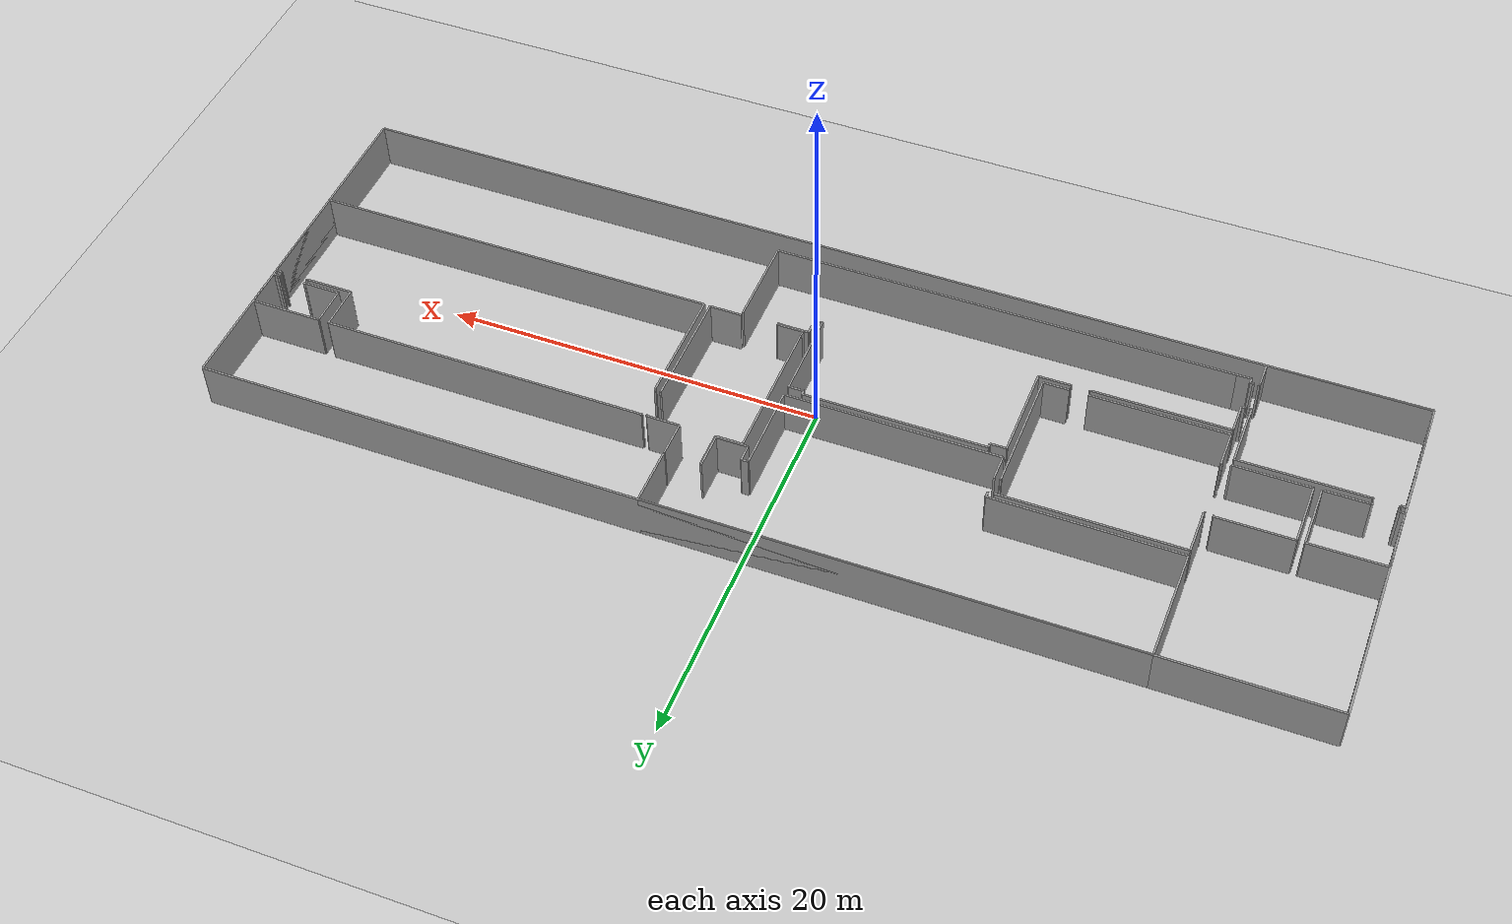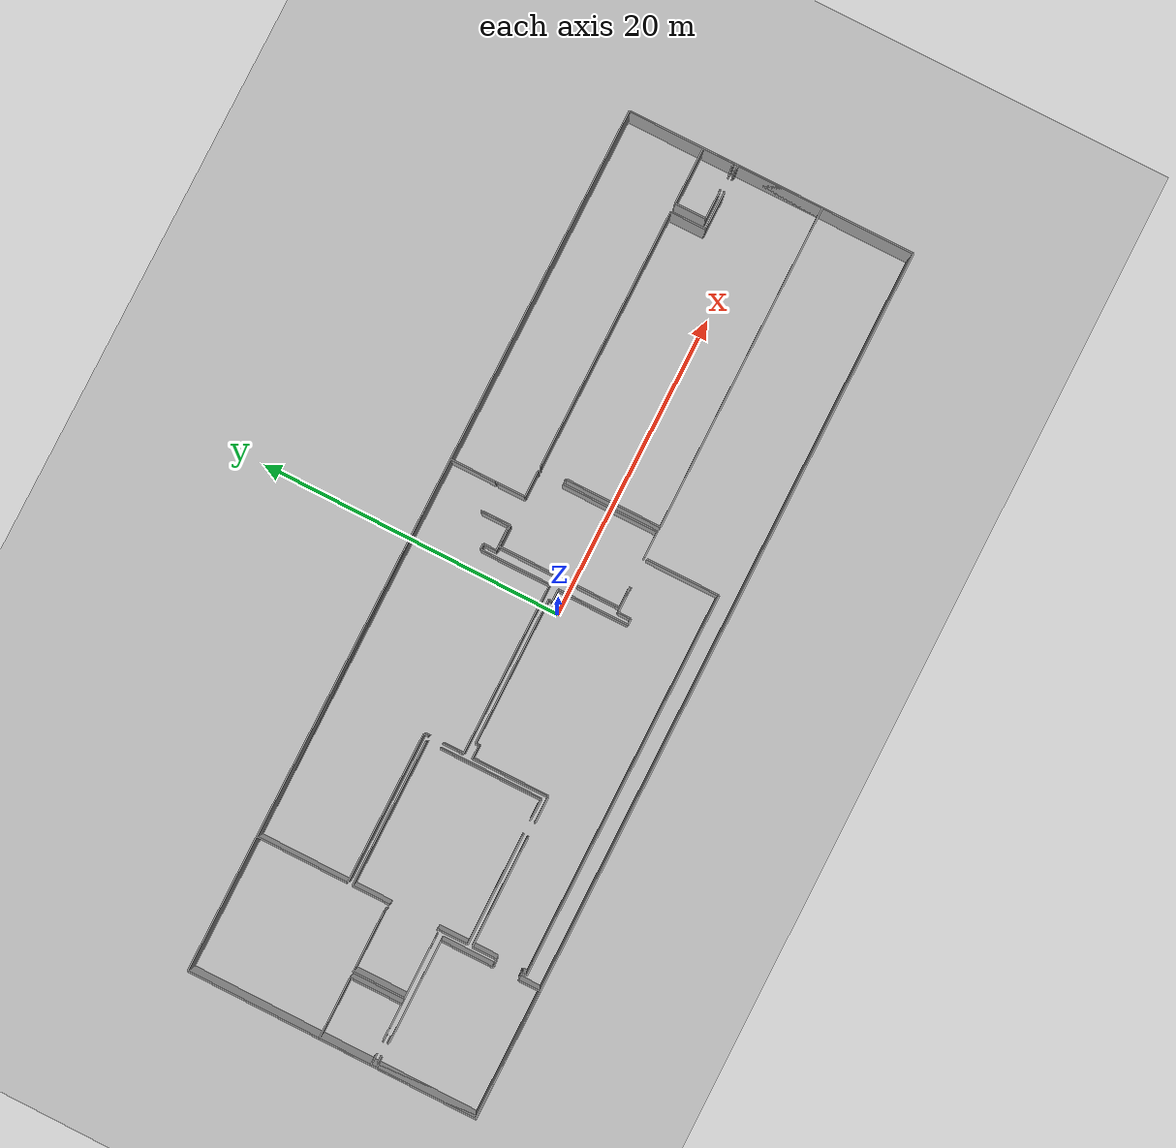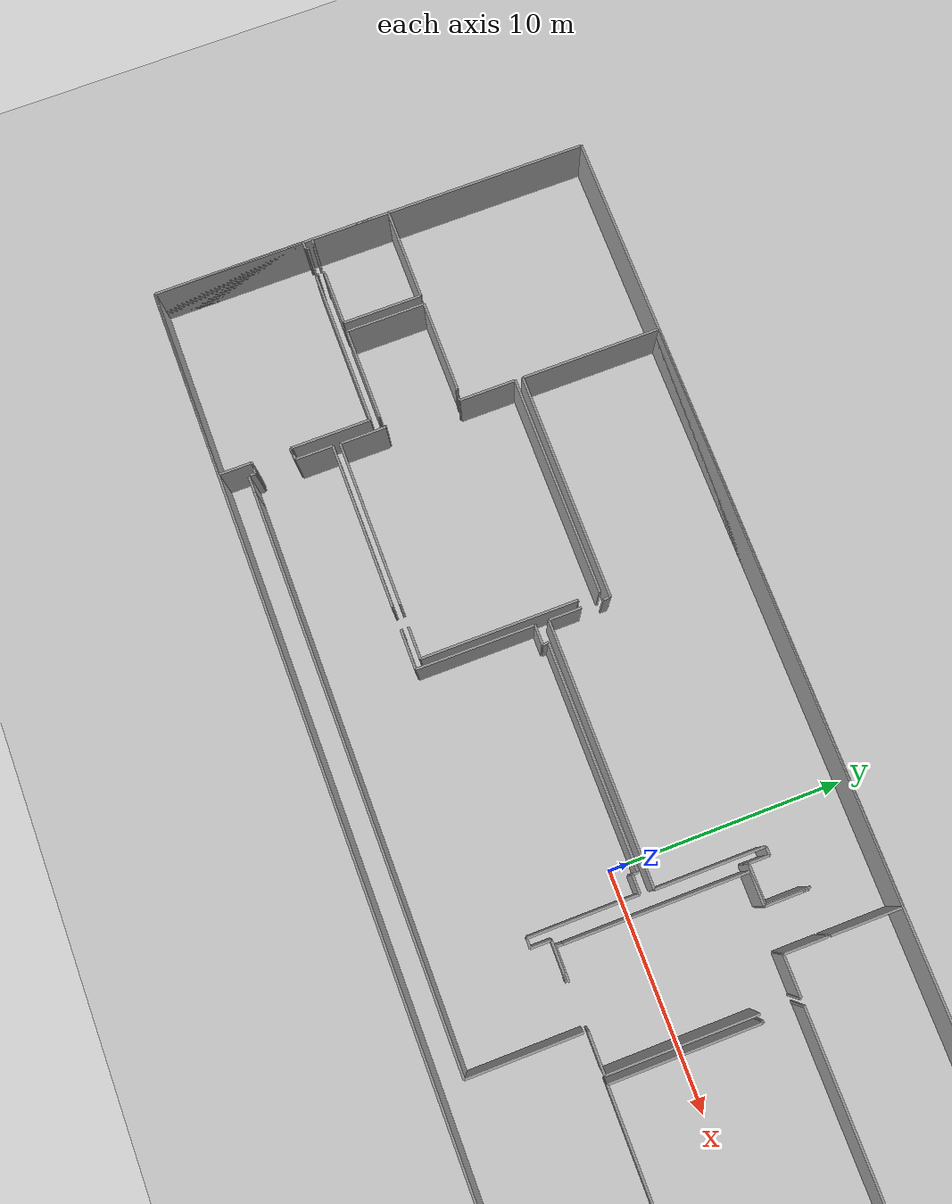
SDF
<sdf version="1.6">
  <world name="default">
    <light name="sun" type="directional">
      <cast_shadows>1</cast_shadows>
      <pose frame="">0 0 10 0 -0 0</pose>
      <diffuse>0.8 0.8 0.8 1</diffuse>
      <specular>0.1 0.1 0.1 1</specular>
      <attenuation>
        <range>1000</range>
        <constant>0.9</constant>
        <linear>0.01</linear>
        <quadratic>0.001</quadratic>
      </attenuation>
      <direction>-0.5 0.5 -1</direction>
    </light>
    <model name="ground_plane">
      <static>1</static>
      <link name="link">
        <collision name="collision">
          <geometry>
            <plane>
              <normal>0 0 1</normal>
              <size>100 100</size>
            </plane>
          </geometry>
          <surface>
            <friction>
              <ode>
                <mu>100</mu>
                <mu2>50</mu2>
              </ode>
              <torsional>
                <ode />
              </torsional>
            </friction>
            <contact>
              <ode />
            </contact>
            <bounce />
          </surface>
          <max_contacts>10</max_contacts>
        </collision>
        <visual name="visual">
          <cast_shadows>0</cast_shadows>
          <geometry>
            <plane>
              <normal>0 0 1</normal>
              <size>100 100</size>
            </plane>
          </geometry>
          <material>
            <script>
              <uri>file://media/materials/scripts/gazebo.material</uri>
              <name>Gazebo/Grey</name>
            </script>
          </material>
        </visual>
        <self_collide>0</self_collide>
        <kinematic>0</kinematic>
        <gravity>1</gravity>
      </link>
    </model>
    <gravity>0 0 -9.8</gravity>
    <magnetic_field>6e-06 2.3e-05 -4.2e-05</magnetic_field>
    <atmosphere type="adiabatic" />
    <physics default="0" name="default_physics" type="ode">
      <max_step_size>0.001</max_step_size>
      <real_time_factor>1</real_time_factor>
      <real_time_update_rate>1000</real_time_update_rate>
    </physics>
    <scene>
      <ambient>0.4 0.4 0.4 1</ambient>
      <background>0.7 0.7 0.7 1</background>
      <shadows>1</shadows>
    </scene>
    <spherical_coordinates>
      <surface_model>EARTH_WGS84</surface_model>
      <latitude_deg>0</latitude_deg>
      <longitude_deg>0</longitude_deg>
      <elevation>0</elevation>
      <heading_deg>0</heading_deg>
    </spherical_coordinates>
  <model name="0510030942_A_40_1_101">
		<static>1</static>
		<link name="Wall_0">
			<collision name="Wall_0_Collision">
				<geometry>
					<box>
						<size>3.39954755732 0.1 2.5</size>
					</box>
				</geometry>
				<pose frame="">1.69977377866 0 1.25 0 0 0</pose>
			</collision>
			<visual name="Wall_0_Visual">
				<pose frame="">1.69977377866 0 1.25 0 0 0</pose>
				<geometry>
					<box>
						<size>3.39954755732 0.1 2.5</size>
					</box>
				</geometry>
				<material>
					<script>
						<uri>file://media/materials/scripts/gazebo.material</uri>
						<name>Gazebo/Grey</name>
					</script>
					<ambient>1 1 1 1</ambient>
				</material>
			</visual>
			<pose frame="">0.00216054089777 -12.1079253724 0 0 0 1.57079632679</pose>
		</link>
		<link name="Wall_1">
			<collision name="Wall_1_Collision">
				<geometry>
					<box>
						<size>3.97514107061 0.1 2.5</size>
					</box>
				</geometry>
				<pose frame="">1.98757053531 0 1.25 0 0 0</pose>
			</collision>
			<visual name="Wall_1_Visual">
				<pose frame="">1.98757053531 0 1.25 0 0 0</pose>
				<geometry>
					<box>
						<size>3.97514107061 0.1 2.5</size>
					</box>
				</geometry>
				<material>
					<script>
						<uri>file://media/materials/scripts/gazebo.material</uri>
						<name>Gazebo/Grey</name>
					</script>
					<ambient>1 1 1 1</ambient>
				</material>
			</visual>
			<pose frame="">0.00216054089777 -8.70837781506 0 0 0 0.0</pose>
		</link>
		<link name="Wall_2">
			<collision name="Wall_2_Collision">
				<geometry>
					<box>
						<size>3.40208937014 0.1 2.5</size>
					</box>
				</geometry>
				<pose frame="">1.70104468507 0 1.25 0 0 0</pose>
			</collision>
			<visual name="Wall_2_Visual">
				<pose frame="">1.70104468507 0 1.25 0 0 0</pose>
				<geometry>
					<box>
						<size>3.40208937014 0.1 2.5</size>
					</box>
				</geometry>
				<material>
					<script>
						<uri>file://media/materials/scripts/gazebo.material</uri>
						<name>Gazebo/Grey</name>
					</script>
					<ambient>1 1 1 1</ambient>
				</material>
			</visual>
			<pose frame="">3.97730161151 -8.70837781506 0 0 0 -1.57079632679</pose>
		</link>
		<link name="Wall_3">
			<collision name="Wall_3_Collision">
				<geometry>
					<box>
						<size>2.34990595293 0.1 2.5</size>
					</box>
				</geometry>
				<pose frame="">1.17495297646 0 1.25 0 0 0</pose>
			</collision>
			<visual name="Wall_3_Visual">
				<pose frame="">1.17495297646 0 1.25 0 0 0</pose>
				<geometry>
					<box>
						<size>2.34990595293 0.1 2.5</size>
					</box>
				</geometry>
				<material>
					<script>
						<uri>file://media/materials/scripts/gazebo.material</uri>
						<name>Gazebo/Grey</name>
					</script>
					<ambient>1 1 1 1</ambient>
				</material>
			</visual>
			<pose frame="">3.97730161151 -12.1104671852 0 0 0 3.14159265359</pose>
		</link>
		<link name="Wall_4">
			<collision name="Wall_4_Collision">
				<geometry>
					<box>
						<size>0.028214122312 0.1 2.5</size>
					</box>
				</geometry>
				<pose frame="">0.014107061156 0 1.25 0 0 0</pose>
			</collision>
			<visual name="Wall_4_Visual">
				<pose frame="">0.014107061156 0 1.25 0 0 0</pose>
				<geometry>
					<box>
						<size>0.028214122312 0.1 2.5</size>
					</box>
				</geometry>
				<material>
					<script>
						<uri>file://media/materials/scripts/gazebo.material</uri>
						<name>Gazebo/Grey</name>
					</script>
					<ambient>1 1 1 1</ambient>
				</material>
			</visual>
			<pose frame="">1.62739565858 -12.1104671852 0 0 0 -1.57079632679</pose>
		</link>
		<link name="Wall_5">
			<collision name="Wall_5_Collision">
				<geometry>
					<box>
						<size>0.103578872452 0.1 2.5</size>
					</box>
				</geometry>
				<pose frame="">0.0517894362259 0 1.25 0 0 0</pose>
			</collision>
			<visual name="Wall_5_Visual">
				<pose frame="">0.0517894362259 0 1.25 0 0 0</pose>
				<geometry>
					<box>
						<size>0.103578872452 0.1 2.5</size>
					</box>
				</geometry>
				<material>
					<script>
						<uri>file://media/materials/scripts/gazebo.material</uri>
						<name>Gazebo/Grey</name>
					</script>
					<ambient>1 1 1 1</ambient>
				</material>
			</visual>
			<pose frame="">1.62739565858 -12.1386813075 0 0 0 3.14159265359</pose>
		</link>
		<link name="Wall_6">
			<collision name="Wall_6_Collision">
				<geometry>
					<box>
						<size>0.12276955925 0.1 2.5</size>
					</box>
				</geometry>
				<pose frame="">0.0613847796248 0 1.25 0 0 0</pose>
			</collision>
			<visual name="Wall_6_Visual">
				<pose frame="">0.0613847796248 0 1.25 0 0 0</pose>
				<geometry>
					<box>
						<size>0.12276955925 0.1 2.5</size>
					</box>
				</geometry>
				<material>
					<script>
						<uri>file://media/materials/scripts/gazebo.material</uri>
						<name>Gazebo/Grey</name>
					</script>
					<ambient>1 1 1 1</ambient>
				</material>
			</visual>
			<pose frame="">0.35623506685 -12.1386813075 0 0 0 3.14159265359</pose>
		</link>
		<link name="Wall_7">
			<collision name="Wall_7_Collision">
				<geometry>
					<box>
						<size>0.0162676020538 0.1 2.5</size>
					</box>
				</geometry>
				<pose frame="">0.00813380102689 0 1.25 0 0 0</pose>
			</collision>
			<visual name="Wall_7_Visual">
				<pose frame="">0.00813380102689 0 1.25 0 0 0</pose>
				<geometry>
					<box>
						<size>0.0162676020538 0.1 2.5</size>
					</box>
				</geometry>
				<material>
					<script>
						<uri>file://media/materials/scripts/gazebo.material</uri>
						<name>Gazebo/Grey</name>
					</script>
					<ambient>1 1 1 1</ambient>
				</material>
			</visual>
			<pose frame="">0.2334655076 -12.1386813075 0 0 0 1.57079632679</pose>
		</link>
		<link name="Wall_8">
			<collision name="Wall_8_Collision">
				<geometry>
					<box>
						<size>0.231758277989 0.1 2.5</size>
					</box>
				</geometry>
				<pose frame="">0.115879138995 0 1.25 0 0 0</pose>
			</collision>
			<visual name="Wall_8_Visual">
				<pose frame="">0.115879138995 0 1.25 0 0 0</pose>
				<geometry>
					<box>
						<size>0.231758277989 0.1 2.5</size>
					</box>
				</geometry>
				<material>
					<script>
						<uri>file://media/materials/scripts/gazebo.material</uri>
						<name>Gazebo/Grey</name>
					</script>
					<ambient>1 1 1 1</ambient>
				</material>
			</visual>
			<pose frame="">0.2334655076 -12.1224137055 0 0 0 3.07903701661</pose>
		</link>
		<link name="Wall_9">
			<collision name="Wall_9_Collision">
				<geometry>
					<box>
						<size>6.52191042652 0.1 2.5</size>
					</box>
				</geometry>
				<pose frame="">3.26095521326 0 1.25 0 0 0</pose>
			</collision>
			<visual name="Wall_9_Visual">
				<pose frame="">3.26095521326 0 1.25 0 0 0</pose>
				<geometry>
					<box>
						<size>6.52191042652 0.1 2.5</size>
					</box>
				</geometry>
				<material>
					<script>
						<uri>file://media/materials/scripts/gazebo.material</uri>
						<name>Gazebo/Grey</name>
					</script>
					<ambient>1 1 1 1</ambient>
				</material>
			</visual>
			<pose frame="">0.0 -19.0235626048 0 0 0 1.57079632679</pose>
		</link>
		<link name="Wall_10">
			<collision name="Wall_10_Collision">
				<geometry>
					<box>
						<size>0.291164658635 0.1 2.5</size>
					</box>
				</geometry>
				<pose frame="">0.145582329317 0 1.25 0 0 0</pose>
			</collision>
			<visual name="Wall_10_Visual">
				<pose frame="">0.145582329317 0 1.25 0 0 0</pose>
				<geometry>
					<box>
						<size>0.291164658635 0.1 2.5</size>
					</box>
				</geometry>
				<material>
					<script>
						<uri>file://media/materials/scripts/gazebo.material</uri>
						<name>Gazebo/Grey</name>
					</script>
					<ambient>1 1 1 1</ambient>
				</material>
			</visual>
			<pose frame="">0.0 -12.5016521783 0 0 0 0.0</pose>
		</link>
		<link name="Wall_11">
			<collision name="Wall_11_Collision">
				<geometry>
					<box>
						<size>0.0829901886025 0.1 2.5</size>
					</box>
				</geometry>
				<pose frame="">0.0414950943013 0 1.25 0 0 0</pose>
			</collision>
			<visual name="Wall_11_Visual">
				<pose frame="">0.0414950943013 0 1.25 0 0 0</pose>
				<geometry>
					<box>
						<size>0.0829901886025 0.1 2.5</size>
					</box>
				</geometry>
				<material>
					<script>
						<uri>file://media/materials/scripts/gazebo.material</uri>
						<name>Gazebo/Grey</name>
					</script>
					<ambient>1 1 1 1</ambient>
				</material>
			</visual>
			<pose frame="">0.291164658635 -12.5016521783 0 0 0 1.57079632679</pose>
		</link>
		<link name="Wall_12">
			<collision name="Wall_12_Collision">
				<geometry>
					<box>
						<size>0.0831172792436 0.1 2.5</size>
					</box>
				</geometry>
				<pose frame="">0.0415586396218 0 1.25 0 0 0</pose>
			</collision>
			<visual name="Wall_12_Visual">
				<pose frame="">0.0415586396218 0 1.25 0 0 0</pose>
				<geometry>
					<box>
						<size>0.0831172792436 0.1 2.5</size>
					</box>
				</geometry>
				<material>
					<script>
						<uri>file://media/materials/scripts/gazebo.material</uri>
						<name>Gazebo/Grey</name>
					</script>
					<ambient>1 1 1 1</ambient>
				</material>
			</visual>
			<pose frame="">0.291164658635 -12.4186619897 0 0 0 0.0</pose>
		</link>
		<link name="Wall_13">
			<collision name="Wall_13_Collision">
				<geometry>
					<box>
						<size>0.0522342534696 0.1 2.5</size>
					</box>
				</geometry>
				<pose frame="">0.0261171267348 0 1.25 0 0 0</pose>
			</collision>
			<visual name="Wall_13_Visual">
				<pose frame="">0.0261171267348 0 1.25 0 0 0</pose>
				<geometry>
					<box>
						<size>0.0522342534696 0.1 2.5</size>
					</box>
				</geometry>
				<material>
					<script>
						<uri>file://media/materials/scripts/gazebo.material</uri>
						<name>Gazebo/Grey</name>
					</script>
					<ambient>1 1 1 1</ambient>
				</material>
			</visual>
			<pose frame="">1.54898073306 -12.4186619897 0 0 0 0.0</pose>
		</link>
		<link name="Wall_14">
			<collision name="Wall_14_Collision">
				<geometry>
					<box>
						<size>0.0748563875756 0.1 2.5</size>
					</box>
				</geometry>
				<pose frame="">0.0374281937878 0 1.25 0 0 0</pose>
			</collision>
			<visual name="Wall_14_Visual">
				<pose frame="">0.0374281937878 0 1.25 0 0 0</pose>
				<geometry>
					<box>
						<size>0.0748563875756 0.1 2.5</size>
					</box>
				</geometry>
				<material>
					<script>
						<uri>file://media/materials/scripts/gazebo.material</uri>
						<name>Gazebo/Grey</name>
					</script>
					<ambient>1 1 1 1</ambient>
				</material>
			</visual>
			<pose frame="">1.60121498653 -12.4186619897 0 0 0 -1.57079632679</pose>
		</link>
		<link name="Wall_15">
			<collision name="Wall_15_Collision">
				<geometry>
					<box>
						<size>6.7271618118 0.1 2.5</size>
					</box>
				</geometry>
				<pose frame="">3.3635809059 0 1.25 0 0 0</pose>
			</collision>
			<visual name="Wall_15_Visual">
				<pose frame="">3.3635809059 0 1.25 0 0 0</pose>
				<geometry>
					<box>
						<size>6.7271618118 0.1 2.5</size>
					</box>
				</geometry>
				<material>
					<script>
						<uri>file://media/materials/scripts/gazebo.material</uri>
						<name>Gazebo/Grey</name>
					</script>
					<ambient>1 1 1 1</ambient>
				</material>
			</visual>
			<pose frame="">1.60121498653 -12.4935183773 0 0 0 0.0</pose>
		</link>
		<link name="Wall_16">
			<collision name="Wall_16_Collision">
				<geometry>
					<box>
						<size>3.41822988155 0.1 2.5</size>
					</box>
				</geometry>
				<pose frame="">1.70911494078 0 1.25 0 0 0</pose>
			</collision>
			<visual name="Wall_16_Visual">
				<pose frame="">1.70911494078 0 1.25 0 0 0</pose>
				<geometry>
					<box>
						<size>3.41822988155 0.1 2.5</size>
					</box>
				</geometry>
				<material>
					<script>
						<uri>file://media/materials/scripts/gazebo.material</uri>
						<name>Gazebo/Grey</name>
					</script>
					<ambient>1 1 1 1</ambient>
				</material>
			</visual>
			<pose frame="">8.32837679833 -12.4935183773 0 0 0 -1.57079632679</pose>
		</link>
		<link name="Wall_17">
			<collision name="Wall_17_Collision">
				<geometry>
					<box>
						<size>0.0514717096233 0.1 2.5</size>
					</box>
				</geometry>
				<pose frame="">0.0257358548117 0 1.25 0 0 0</pose>
			</collision>
			<visual name="Wall_17_Visual">
				<pose frame="">0.0257358548117 0 1.25 0 0 0</pose>
				<geometry>
					<box>
						<size>0.0514717096233 0.1 2.5</size>
					</box>
				</geometry>
				<material>
					<script>
						<uri>file://media/materials/scripts/gazebo.material</uri>
						<name>Gazebo/Grey</name>
					</script>
					<ambient>1 1 1 1</ambient>
				</material>
			</visual>
			<pose frame="">8.32837679833 -15.9117482589 0 0 0 0.0</pose>
		</link>
		<link name="Wall_18">
			<collision name="Wall_18_Collision">
				<geometry>
					<box>
						<size>0.0913781709115 0.1 2.5</size>
					</box>
				</geometry>
				<pose frame="">0.0456890854557 0 1.25 0 0 0</pose>
			</collision>
			<visual name="Wall_18_Visual">
				<pose frame="">0.0456890854557 0 1.25 0 0 0</pose>
				<geometry>
					<box>
						<size>0.0913781709115 0.1 2.5</size>
					</box>
				</geometry>
				<material>
					<script>
						<uri>file://media/materials/scripts/gazebo.material</uri>
						<name>Gazebo/Grey</name>
					</script>
					<ambient>1 1 1 1</ambient>
				</material>
			</visual>
			<pose frame="">8.37984850796 -15.9117482589 0 0 0 -1.57079632679</pose>
		</link>
		<link name="Wall_19">
			<collision name="Wall_19_Collision">
				<geometry>
					<box>
						<size>0.0721874841137 0.1 2.5</size>
					</box>
				</geometry>
				<pose frame="">0.0360937420568 0 1.25 0 0 0</pose>
			</collision>
			<visual name="Wall_19_Visual">
				<pose frame="">0.0360937420568 0 1.25 0 0 0</pose>
				<geometry>
					<box>
						<size>0.0721874841137 0.1 2.5</size>
					</box>
				</geometry>
				<material>
					<script>
						<uri>file://media/materials/scripts/gazebo.material</uri>
						<name>Gazebo/Grey</name>
					</script>
					<ambient>1 1 1 1</ambient>
				</material>
			</visual>
			<pose frame="">8.37984850796 -17.5739667531 0 0 0 -1.57079632679</pose>
		</link>
		<link name="Wall_20">
			<collision name="Wall_20_Collision">
				<geometry>
					<box>
						<size>0.0322810228255 0.1 2.5</size>
					</box>
				</geometry>
				<pose frame="">0.0161405114127 0 1.25 0 0 0</pose>
			</collision>
			<visual name="Wall_20_Visual">
				<pose frame="">0.0161405114127 0 1.25 0 0 0</pose>
				<geometry>
					<box>
						<size>0.0322810228255 0.1 2.5</size>
					</box>
				</geometry>
				<material>
					<script>
						<uri>file://media/materials/scripts/gazebo.material</uri>
						<name>Gazebo/Grey</name>
					</script>
					<ambient>1 1 1 1</ambient>
				</material>
			</visual>
			<pose frame="">8.37984850796 -17.6461542372 0 0 0 3.14159265359</pose>
		</link>
		<link name="Wall_21">
			<collision name="Wall_21_Collision">
				<geometry>
					<box>
						<size>1.39405724162 0.1 2.5</size>
					</box>
				</geometry>
				<pose frame="">0.697028620812 0 1.25 0 0 0</pose>
			</collision>
			<visual name="Wall_21_Visual">
				<pose frame="">0.697028620812 0 1.25 0 0 0</pose>
				<geometry>
					<box>
						<size>1.39405724162 0.1 2.5</size>
					</box>
				</geometry>
				<material>
					<script>
						<uri>file://media/materials/scripts/gazebo.material</uri>
						<name>Gazebo/Grey</name>
					</script>
					<ambient>1 1 1 1</ambient>
				</material>
			</visual>
			<pose frame="">8.34756748513 -17.6461542372 0 0 0 -1.57079632679</pose>
		</link>
		<link name="Wall_22">
			<collision name="Wall_22_Collision">
				<geometry>
					<box>
						<size>8.34758408786 0.1 2.5</size>
					</box>
				</geometry>
				<pose frame="">4.17379204393 0 1.25 0 0 0</pose>
			</collision>
			<visual name="Wall_22_Visual">
				<pose frame="">4.17379204393 0 1.25 0 0 0</pose>
				<geometry>
					<box>
						<size>8.34758408786 0.1 2.5</size>
					</box>
				</geometry>
				<material>
					<script>
						<uri>file://media/materials/scripts/gazebo.material</uri>
						<name>Gazebo/Grey</name>
					</script>
					<ambient>1 1 1 1</ambient>
				</material>
			</visual>
			<pose frame="">8.34756748513 -19.0402114788 0 0 0 3.13959819809</pose>
		</link>
		<link name="Wall_23">
			<collision name="Wall_23_Collision">
				<geometry>
					<box>
						<size>3.39598901937 0.1 2.5</size>
					</box>
				</geometry>
				<pose frame="">1.69799450968 0 1.25 0 0 0</pose>
			</collision>
			<visual name="Wall_23_Visual">
				<pose frame="">1.69799450968 0 1.25 0 0 0</pose>
				<geometry>
					<box>
						<size>3.39598901937 0.1 2.5</size>
					</box>
				</geometry>
				<material>
					<script>
						<uri>file://media/materials/scripts/gazebo.material</uri>
						<name>Gazebo/Grey</name>
					</script>
					<ambient>1 1 1 1</ambient>
				</material>
			</visual>
			<pose frame="">4.37001169234 -12.1010624778 0 0 0 1.57079632679</pose>
		</link>
		<link name="Wall_24">
			<collision name="Wall_24_Collision">
				<geometry>
					<box>
						<size>3.98708759087 0.1 2.5</size>
					</box>
				</geometry>
				<pose frame="">1.99354379543 0 1.25 0 0 0</pose>
			</collision>
			<visual name="Wall_24_Visual">
				<pose frame="">1.99354379543 0 1.25 0 0 0</pose>
				<geometry>
					<box>
						<size>3.98708759087 0.1 2.5</size>
					</box>
				</geometry>
				<material>
					<script>
						<uri>file://media/materials/scripts/gazebo.material</uri>
						<name>Gazebo/Grey</name>
					</script>
					<ambient>1 1 1 1</ambient>
				</material>
			</visual>
			<pose frame="">4.37001169234 -8.70507345839 0 0 0 0.0</pose>
		</link>
		<link name="Wall_25">
			<collision name="Wall_25_Collision">
				<geometry>
					<box>
						<size>0.0804483757816 0.1 2.5</size>
					</box>
				</geometry>
				<pose frame="">0.0402241878908 0 1.25 0 0 0</pose>
			</collision>
			<visual name="Wall_25_Visual">
				<pose frame="">0.0402241878908 0 1.25 0 0 0</pose>
				<geometry>
					<box>
						<size>0.0804483757816 0.1 2.5</size>
					</box>
				</geometry>
				<material>
					<script>
						<uri>file://media/materials/scripts/gazebo.material</uri>
						<name>Gazebo/Grey</name>
					</script>
					<ambient>1 1 1 1</ambient>
				</material>
			</visual>
			<pose frame="">8.35709928321 -8.70507345839 0 0 0 -1.57079632679</pose>
		</link>
		<link name="Wall_26">
			<collision name="Wall_26_Collision">
				<geometry>
					<box>
						<size>0.0540135224442 0.1 2.5</size>
					</box>
				</geometry>
				<pose frame="">0.0270067612221 0 1.25 0 0 0</pose>
			</collision>
			<visual name="Wall_26_Visual">
				<pose frame="">0.0270067612221 0 1.25 0 0 0</pose>
				<geometry>
					<box>
						<size>0.0540135224442 0.1 2.5</size>
					</box>
				</geometry>
				<material>
					<script>
						<uri>file://media/materials/scripts/gazebo.material</uri>
						<name>Gazebo/Grey</name>
					</script>
					<ambient>1 1 1 1</ambient>
				</material>
			</visual>
			<pose frame="">8.35709928321 -12.0437445986 0 0 0 -1.57079632679</pose>
		</link>
		<link name="Wall_27">
			<collision name="Wall_27_Collision">
				<geometry>
					<box>
						<size>3.98708896014 0.1 2.5</size>
					</box>
				</geometry>
				<pose frame="">1.99354448007 0 1.25 0 0 0</pose>
			</collision>
			<visual name="Wall_27_Visual">
				<pose frame="">1.99354448007 0 1.25 0 0 0</pose>
				<geometry>
					<box>
						<size>3.98708896014 0.1 2.5</size>
					</box>
				</geometry>
				<material>
					<script>
						<uri>file://media/materials/scripts/gazebo.material</uri>
						<name>Gazebo/Grey</name>
					</script>
					<ambient>1 1 1 1</ambient>
				</material>
			</visual>
			<pose frame="">8.35709928321 -12.0977581211 0 0 0 -3.14076388928</pose>
		</link>
		<link name="Wall_28">
			<collision name="Wall_28_Collision">
				<geometry>
					<box>
						<size>1.97397183671 0.1 2.5</size>
					</box>
				</geometry>
				<pose frame="">0.986985918357 0 1.25 0 0 0</pose>
			</collision>
			<visual name="Wall_28_Visual">
				<pose frame="">0.986985918357 0 1.25 0 0 0</pose>
				<geometry>
					<box>
						<size>1.97397183671 0.1 2.5</size>
					</box>
				</geometry>
				<material>
					<script>
						<uri>file://media/materials/scripts/gazebo.material</uri>
						<name>Gazebo/Grey</name>
					</script>
					<ambient>1 1 1 1</ambient>
				</material>
			</visual>
			<pose frame="">8.85122769559 -13.9839103248 0 0 0 1.57079632679</pose>
		</link>
		<link name="Wall_29">
			<collision name="Wall_29_Collision">
				<geometry>
					<box>
						<size>0.0862945452697 0.1 2.5</size>
					</box>
				</geometry>
				<pose frame="">0.0431472726348 0 1.25 0 0 0</pose>
			</collision>
			<visual name="Wall_29_Visual">
				<pose frame="">0.0431472726348 0 1.25 0 0 0</pose>
				<geometry>
					<box>
						<size>0.0862945452697 0.1 2.5</size>
					</box>
				</geometry>
				<material>
					<script>
						<uri>file://media/materials/scripts/gazebo.material</uri>
						<name>Gazebo/Grey</name>
					</script>
					<ambient>1 1 1 1</ambient>
				</material>
			</visual>
			<pose frame="">8.85122769559 -12.0099384881 0 0 0 3.14159265359</pose>
		</link>
		<link name="Wall_30">
			<collision name="Wall_30_Collision">
				<geometry>
					<box>
						<size>0.0742209343704 0.1 2.5</size>
					</box>
				</geometry>
				<pose frame="">0.0371104671852 0 1.25 0 0 0</pose>
			</collision>
			<visual name="Wall_30_Visual">
				<pose frame="">0.0371104671852 0 1.25 0 0 0</pose>
				<geometry>
					<box>
						<size>0.0742209343704 0.1 2.5</size>
					</box>
				</geometry>
				<material>
					<script>
						<uri>file://media/materials/scripts/gazebo.material</uri>
						<name>Gazebo/Grey</name>
					</script>
					<ambient>1 1 1 1</ambient>
				</material>
			</visual>
			<pose frame="">8.76493315032 -8.78691983122 0 0 0 0.0</pose>
		</link>
		<link name="Wall_31">
			<collision name="Wall_31_Collision">
				<geometry>
					<box>
						<size>2.43797976717 0.1 2.5</size>
					</box>
				</geometry>
				<pose frame="">1.21898988358 0 1.25 0 0 0</pose>
			</collision>
			<visual name="Wall_31_Visual">
				<pose frame="">1.21898988358 0 1.25 0 0 0</pose>
				<geometry>
					<box>
						<size>2.43797976717 0.1 2.5</size>
					</box>
				</geometry>
				<material>
					<script>
						<uri>file://media/materials/scripts/gazebo.material</uri>
						<name>Gazebo/Grey</name>
					</script>
					<ambient>1 1 1 1</ambient>
				</material>
			</visual>
			<pose frame="">8.83915408469 -8.78691983122 0 0 0 1.57079632679</pose>
		</link>
		<link name="Wall_32">
			<collision name="Wall_32_Collision">
				<geometry>
					<box>
						<size>9.54094860454 0.1 2.5</size>
					</box>
				</geometry>
				<pose frame="">4.77047430227 0 1.25 0 0 0</pose>
			</collision>
			<visual name="Wall_32_Visual">
				<pose frame="">4.77047430227 0 1.25 0 0 0</pose>
				<geometry>
					<box>
						<size>9.54094860454 0.1 2.5</size>
					</box>
				</geometry>
				<material>
					<script>
						<uri>file://media/materials/scripts/gazebo.material</uri>
						<name>Gazebo/Grey</name>
					</script>
					<ambient>1 1 1 1</ambient>
				</material>
			</visual>
			<pose frame="">8.83915408469 -6.34894006405 0 0 0 0.0</pose>
		</link>
		<link name="Wall_33">
			<collision name="Wall_33_Collision">
				<geometry>
					<box>
						<size>0.0437191805195 0.1 2.5</size>
					</box>
				</geometry>
				<pose frame="">0.0218595902598 0 1.25 0 0 0</pose>
			</collision>
			<visual name="Wall_33_Visual">
				<pose frame="">0.0218595902598 0 1.25 0 0 0</pose>
				<geometry>
					<box>
						<size>0.0437191805195 0.1 2.5</size>
					</box>
				</geometry>
				<material>
					<script>
						<uri>file://media/materials/scripts/gazebo.material</uri>
						<name>Gazebo/Grey</name>
					</script>
					<ambient>1 1 1 1</ambient>
				</material>
			</visual>
			<pose frame="">18.3801026892 -7.26259468253 0 0 0 -1.57079632679</pose>
		</link>
		<link name="Wall_34">
			<collision name="Wall_34_Collision">
				<geometry>
					<box>
						<size>0.0180468710284 0.1 2.5</size>
					</box>
				</geometry>
				<pose frame="">0.00902343551421 0 1.25 0 0 0</pose>
			</collision>
			<visual name="Wall_34_Visual">
				<pose frame="">0.00902343551421 0 1.25 0 0 0</pose>
				<geometry>
					<box>
						<size>0.0180468710284 0.1 2.5</size>
					</box>
				</geometry>
				<material>
					<script>
						<uri>file://media/materials/scripts/gazebo.material</uri>
						<name>Gazebo/Grey</name>
					</script>
					<ambient>1 1 1 1</ambient>
				</material>
			</visual>
			<pose frame="">18.3801026892 -7.30631386305 0 0 0 3.14159265359</pose>
		</link>
		<link name="Wall_35">
			<collision name="Wall_35_Collision">
				<geometry>
					<box>
						<size>6.66933557013 0.1 2.5</size>
					</box>
				</geometry>
				<pose frame="">3.33466778506 0 1.25 0 0 0</pose>
			</collision>
			<visual name="Wall_35_Visual">
				<pose frame="">3.33466778506 0 1.25 0 0 0</pose>
				<geometry>
					<box>
						<size>6.66933557013 0.1 2.5</size>
					</box>
				</geometry>
				<material>
					<script>
						<uri>file://media/materials/scripts/gazebo.material</uri>
						<name>Gazebo/Grey</name>
					</script>
					<ambient>1 1 1 1</ambient>
				</material>
			</visual>
			<pose frame="">18.3620558182 -7.30631386305 0 0 0 -1.57079632679</pose>
		</link>
		<link name="Wall_36">
			<collision name="Wall_36_Collision">
				<geometry>
					<box>
						<size>1.37283310457 0.1 2.5</size>
					</box>
				</geometry>
				<pose frame="">0.686416552285 0 1.25 0 0 0</pose>
			</collision>
			<visual name="Wall_36_Visual">
				<pose frame="">0.686416552285 0 1.25 0 0 0</pose>
				<geometry>
					<box>
						<size>1.37283310457 0.1 2.5</size>
					</box>
				</geometry>
				<material>
					<script>
						<uri>file://media/materials/scripts/gazebo.material</uri>
						<name>Gazebo/Grey</name>
					</script>
					<ambient>1 1 1 1</ambient>
				</material>
			</visual>
			<pose frame="">18.3620558182 -13.9756494332 0 0 0 3.14159265359</pose>
		</link>
		<link name="Wall_37">
			<collision name="Wall_37_Collision">
				<geometry>
					<box>
						<size>7.17516107695 0.1 2.5</size>
					</box>
				</geometry>
				<pose frame="">3.58758053847 0 1.25 0 0 0</pose>
			</collision>
			<visual name="Wall_37_Visual">
				<pose frame="">3.58758053847 0 1.25 0 0 0</pose>
				<geometry>
					<box>
						<size>7.17516107695 0.1 2.5</size>
					</box>
				</geometry>
				<material>
					<script>
						<uri>file://media/materials/scripts/gazebo.material</uri>
						<name>Gazebo/Grey</name>
					</script>
					<ambient>1 1 1 1</ambient>
				</material>
			</visual>
			<pose frame="">16.0263840171 -13.9756494332 0 0 0 -3.1404413354</pose>
		</link>
		<link name="Wall_38">
			<collision name="Wall_38_Collision">
				<geometry>
					<box>
						<size>6.02053784759 0.1 2.5</size>
					</box>
				</geometry>
				<pose frame="">3.0102689238 0 1.25 0 0 0</pose>
			</collision>
			<visual name="Wall_38_Visual">
				<pose frame="">3.0102689238 0 1.25 0 0 0</pose>
				<geometry>
					<box>
						<size>6.02053784759 0.1 2.5</size>
					</box>
				</geometry>
				<material>
					<script>
						<uri>file://media/materials/scripts/gazebo.material</uri>
						<name>Gazebo/Grey</name>
					</script>
					<ambient>1 1 1 1</ambient>
				</material>
			</visual>
			<pose frame="">8.84614406995 -6.02053784759 0 0 0 1.57079632679</pose>
		</link>
		<link name="Wall_39">
			<collision name="Wall_39_Collision">
				<geometry>
					<box>
						<size>25.1155253927 0.1 2.5</size>
					</box>
				</geometry>
				<pose frame="">12.5577626964 0 1.25 0 0 0</pose>
			</collision>
			<visual name="Wall_39_Visual">
				<pose frame="">12.5577626964 0 1.25 0 0 0</pose>
				<geometry>
					<box>
						<size>25.1155253927 0.1 2.5</size>
					</box>
				</geometry>
				<material>
					<script>
						<uri>file://media/materials/scripts/gazebo.material</uri>
						<name>Gazebo/Grey</name>
					</script>
					<ambient>1 1 1 1</ambient>
				</material>
			</visual>
			<pose frame="">8.84614406995 -0.0 0 0 0 0.0</pose>
		</link>
		<link name="Wall_40">
			<collision name="Wall_40_Collision">
				<geometry>
					<box>
						<size>3.01192110213 0.1 2.5</size>
					</box>
				</geometry>
				<pose frame="">1.50596055107 0 1.25 0 0 0</pose>
			</collision>
			<visual name="Wall_40_Visual">
				<pose frame="">1.50596055107 0 1.25 0 0 0</pose>
				<geometry>
					<box>
						<size>3.01192110213 0.1 2.5</size>
					</box>
				</geometry>
				<material>
					<script>
						<uri>file://media/materials/scripts/gazebo.material</uri>
						<name>Gazebo/Grey</name>
					</script>
					<ambient>1 1 1 1</ambient>
				</material>
			</visual>
			<pose frame="">33.9616694627 -0.0 0 0 0 -1.57079632679</pose>
		</link>
		<link name="Wall_41">
			<collision name="Wall_41_Collision">
				<geometry>
					<box>
						<size>1.88500838798 0.1 2.5</size>
					</box>
				</geometry>
				<pose frame="">0.942504193991 0 1.25 0 0 0</pose>
			</collision>
			<visual name="Wall_41_Visual">
				<pose frame="">0.942504193991 0 1.25 0 0 0</pose>
				<geometry>
					<box>
						<size>1.88500838798 0.1 2.5</size>
					</box>
				</geometry>
				<material>
					<script>
						<uri>file://media/materials/scripts/gazebo.material</uri>
						<name>Gazebo/Grey</name>
					</script>
					<ambient>1 1 1 1</ambient>
				</material>
			</visual>
			<pose frame="">32.0152762951 -3.01192110213 0 0 0 -1.57079632679</pose>
		</link>
		<link name="Wall_42">
			<collision name="Wall_42_Collision">
				<geometry>
					<box>
						<size>1.67187738295 0.1 2.5</size>
					</box>
				</geometry>
				<pose frame="">0.835938691475 0 1.25 0 0 0</pose>
			</collision>
			<visual name="Wall_42_Visual">
				<pose frame="">0.835938691475 0 1.25 0 0 0</pose>
				<geometry>
					<box>
						<size>1.67187738295 0.1 2.5</size>
					</box>
				</geometry>
				<material>
					<script>
						<uri>file://media/materials/scripts/gazebo.material</uri>
						<name>Gazebo/Grey</name>
					</script>
					<ambient>1 1 1 1</ambient>
				</material>
			</visual>
			<pose frame="">32.0152762951 -4.89692949011 0 0 0 3.14159265359</pose>
		</link>
		<link name="Wall_43">
			<collision name="Wall_43_Collision">
				<geometry>
					<box>
						<size>0.869681256672 0.1 2.5</size>
					</box>
				</geometry>
				<pose frame="">0.434840628336 0 1.25 0 0 0</pose>
			</collision>
			<visual name="Wall_43_Visual">
				<pose frame="">0.434840628336 0 1.25 0 0 0</pose>
				<geometry>
					<box>
						<size>0.869681256672 0.1 2.5</size>
					</box>
				</geometry>
				<material>
					<script>
						<uri>file://media/materials/scripts/gazebo.material</uri>
						<name>Gazebo/Grey</name>
					</script>
					<ambient>1 1 1 1</ambient>
				</material>
			</visual>
			<pose frame="">30.3433989121 -4.89692949011 0 0 0 1.57079632679</pose>
		</link>
		<link name="Wall_44">
			<collision name="Wall_44_Collision">
				<geometry>
					<box>
						<size>0.362716689543 0.1 2.5</size>
					</box>
				</geometry>
				<pose frame="">0.181358344771 0 1.25 0 0 0</pose>
			</collision>
			<visual name="Wall_44_Visual">
				<pose frame="">0.181358344771 0 1.25 0 0 0</pose>
				<geometry>
					<box>
						<size>0.362716689543 0.1 2.5</size>
					</box>
				</geometry>
				<material>
					<script>
						<uri>file://media/materials/scripts/gazebo.material</uri>
						<name>Gazebo/Grey</name>
					</script>
					<ambient>1 1 1 1</ambient>
				</material>
			</visual>
			<pose frame="">30.3433989121 -4.02724823344 0 0 0 3.14159265359</pose>
		</link>
		<link name="Wall_45">
			<collision name="Wall_45_Collision">
				<geometry>
					<box>
						<size>4.62927660007 0.1 2.5</size>
					</box>
				</geometry>
				<pose frame="">2.31463830004 0 1.25 0 0 0</pose>
			</collision>
			<visual name="Wall_45_Visual">
				<pose frame="">2.31463830004 0 1.25 0 0 0</pose>
				<geometry>
					<box>
						<size>4.62927660007 0.1 2.5</size>
					</box>
				</geometry>
				<material>
					<script>
						<uri>file://media/materials/scripts/gazebo.material</uri>
						<name>Gazebo/Grey</name>
					</script>
					<ambient>1 1 1 1</ambient>
				</material>
			</visual>
			<pose frame="">29.9806822226 -4.02724823344 0 0 0 -1.57079632679</pose>
		</link>
		<link name="Wall_46">
			<collision name="Wall_46_Collision">
				<geometry>
					<box>
						<size>11.2853947435 0.1 2.5</size>
					</box>
				</geometry>
				<pose frame="">5.64269737177 0 1.25 0 0 0</pose>
			</collision>
			<visual name="Wall_46_Visual">
				<pose frame="">5.64269737177 0 1.25 0 0 0</pose>
				<geometry>
					<box>
						<size>11.2853947435 0.1 2.5</size>
					</box>
				</geometry>
				<material>
					<script>
						<uri>file://media/materials/scripts/gazebo.material</uri>
						<name>Gazebo/Grey</name>
					</script>
					<ambient>1 1 1 1</ambient>
				</material>
			</visual>
			<pose frame="">29.9806822226 -8.65652483351 0 0 0 3.14159265359</pose>
		</link>
		<link name="Wall_47">
			<collision name="Wall_47_Collision">
				<geometry>
					<box>
						<size>1.38554216867 0.1 2.5</size>
					</box>
				</geometry>
				<pose frame="">0.692771084337 0 1.25 0 0 0</pose>
			</collision>
			<visual name="Wall_47_Visual">
				<pose frame="">0.692771084337 0 1.25 0 0 0</pose>
				<geometry>
					<box>
						<size>1.38554216867 0.1 2.5</size>
					</box>
				</geometry>
				<material>
					<script>
						<uri>file://media/materials/scripts/gazebo.material</uri>
						<name>Gazebo/Grey</name>
					</script>
					<ambient>1 1 1 1</ambient>
				</material>
			</visual>
			<pose frame="">18.695287479 -8.65652483351 0 0 0 1.57079632679</pose>
		</link>
		<link name="Wall_48">
			<collision name="Wall_48_Collision">
				<geometry>
					<box>
						<size>0.315947333638 0.1 2.5</size>
					</box>
				</geometry>
				<pose frame="">0.157973666819 0 1.25 0 0 0</pose>
			</collision>
			<visual name="Wall_48_Visual">
				<pose frame="">0.157973666819 0 1.25 0 0 0</pose>
				<geometry>
					<box>
						<size>0.315947333638 0.1 2.5</size>
					</box>
				</geometry>
				<material>
					<script>
						<uri>file://media/materials/scripts/gazebo.material</uri>
						<name>Gazebo/Grey</name>
					</script>
					<ambient>1 1 1 1</ambient>
				</material>
			</visual>
			<pose frame="">18.695287479 -6.34588988867 0 0 0 1.57079632679</pose>
		</link>
		<link name="Wall_49">
			<collision name="Wall_49_Collision">
				<geometry>
					<box>
						<size>9.84914789924 0.1 2.5</size>
					</box>
				</geometry>
				<pose frame="">4.92457394962 0 1.25 0 0 0</pose>
			</collision>
			<visual name="Wall_49_Visual">
				<pose frame="">4.92457394962 0 1.25 0 0 0</pose>
				<geometry>
					<box>
						<size>9.84914789924 0.1 2.5</size>
					</box>
				</geometry>
				<material>
					<script>
						<uri>file://media/materials/scripts/gazebo.material</uri>
						<name>Gazebo/Grey</name>
					</script>
					<ambient>1 1 1 1</ambient>
				</material>
			</visual>
			<pose frame="">18.695287479 -6.02994255503 0 0 0 3.14063777821</pose>
		</link>
		<link name="Wall_50">
			<collision name="Wall_50_Collision">
				<geometry>
					<box>
						<size>0.745259519089 0.1 2.5</size>
					</box>
				</geometry>
				<pose frame="">0.372629759545 0 1.25 0 0 0</pose>
			</collision>
			<visual name="Wall_50_Visual">
				<pose frame="">0.372629759545 0 1.25 0 0 0</pose>
				<geometry>
					<box>
						<size>0.745259519089 0.1 2.5</size>
					</box>
				</geometry>
				<material>
					<script>
						<uri>file://media/materials/scripts/gazebo.material</uri>
						<name>Gazebo/Grey</name>
					</script>
					<ambient>1 1 1 1</ambient>
				</material>
			</visual>
			<pose frame="">9.57056072391 -17.9064358701 0 0 0 3.14159265359</pose>
		</link>
		<link name="Wall_51">
			<collision name="Wall_51_Collision">
				<geometry>
					<box>
						<size>0.286589395557 0.1 2.5</size>
					</box>
				</geometry>
				<pose frame="">0.143294697778 0 1.25 0 0 0</pose>
			</collision>
			<visual name="Wall_51_Visual">
				<pose frame="">0.143294697778 0 1.25 0 0 0</pose>
				<geometry>
					<box>
						<size>0.286589395557 0.1 2.5</size>
					</box>
				</geometry>
				<material>
					<script>
						<uri>file://media/materials/scripts/gazebo.material</uri>
						<name>Gazebo/Grey</name>
					</script>
					<ambient>1 1 1 1</ambient>
				</material>
			</visual>
			<pose frame="">8.82530120482 -17.9064358701 0 0 0 1.57079632679</pose>
		</link>
		<link name="Wall_52">
			<collision name="Wall_52_Collision">
				<geometry>
					<box>
						<size>0.173097453104 0.1 2.5</size>
					</box>
				</geometry>
				<pose frame="">0.0865487265518 0 1.25 0 0 0</pose>
			</collision>
			<visual name="Wall_52_Visual">
				<pose frame="">0.0865487265518 0 1.25 0 0 0</pose>
				<geometry>
					<box>
						<size>0.173097453104 0.1 2.5</size>
					</box>
				</geometry>
				<material>
					<script>
						<uri>file://media/materials/scripts/gazebo.material</uri>
						<name>Gazebo/Grey</name>
					</script>
					<ambient>1 1 1 1</ambient>
				</material>
			</visual>
			<pose frame="">8.82530120482 -17.6198464745 0 0 0 3.14159265359</pose>
		</link>
		<link name="Wall_53">
			<collision name="Wall_53_Collision">
				<geometry>
					<box>
						<size>0.0723145747547 0.1 2.5</size>
					</box>
				</geometry>
				<pose frame="">0.0361572873774 0 1.25 0 0 0</pose>
			</collision>
			<visual name="Wall_53_Visual">
				<pose frame="">0.0361572873774 0 1.25 0 0 0</pose>
				<geometry>
					<box>
						<size>0.0723145747547 0.1 2.5</size>
					</box>
				</geometry>
				<material>
					<script>
						<uri>file://media/materials/scripts/gazebo.material</uri>
						<name>Gazebo/Grey</name>
					</script>
					<ambient>1 1 1 1</ambient>
				</material>
			</visual>
			<pose frame="">8.65220375172 -17.6198464745 0 0 0 1.57079632679</pose>
		</link>
		<link name="Wall_54">
			<collision name="Wall_54_Collision">
				<geometry>
					<box>
						<size>0.0671038584719 0.1 2.5</size>
					</box>
				</geometry>
				<pose frame="">0.0335519292359 0 1.25 0 0 0</pose>
			</collision>
			<visual name="Wall_54_Visual">
				<pose frame="">0.0335519292359 0 1.25 0 0 0</pose>
				<geometry>
					<box>
						<size>0.0671038584719 0.1 2.5</size>
					</box>
				</geometry>
				<material>
					<script>
						<uri>file://media/materials/scripts/gazebo.material</uri>
						<name>Gazebo/Grey</name>
					</script>
					<ambient>1 1 1 1</ambient>
				</material>
			</visual>
			<pose frame="">8.65220375172 -15.9791062986 0 0 0 1.57079632679</pose>
		</link>
		<link name="Wall_55">
			<collision name="Wall_55_Collision">
				<geometry>
					<box>
						<size>0.184154338874 0.1 2.5</size>
					</box>
				</geometry>
				<pose frame="">0.0920771694372 0 1.25 0 0 0</pose>
			</collision>
			<visual name="Wall_55_Visual">
				<pose frame="">0.0920771694372 0 1.25 0 0 0</pose>
				<geometry>
					<box>
						<size>0.184154338874 0.1 2.5</size>
					</box>
				</geometry>
				<material>
					<script>
						<uri>file://media/materials/scripts/gazebo.material</uri>
						<name>Gazebo/Grey</name>
					</script>
					<ambient>1 1 1 1</ambient>
				</material>
			</visual>
			<pose frame="">8.65220375172 -15.9120024401 0 0 0 0.0</pose>
		</link>
		<link name="Wall_56">
			<collision name="Wall_56_Collision">
				<geometry>
					<box>
						<size>1.61646586345 0.1 2.5</size>
					</box>
				</geometry>
				<pose frame="">0.808232931727 0 1.25 0 0 0</pose>
			</collision>
			<visual name="Wall_56_Visual">
				<pose frame="">0.808232931727 0 1.25 0 0 0</pose>
				<geometry>
					<box>
						<size>1.61646586345 0.1 2.5</size>
					</box>
				</geometry>
				<material>
					<script>
						<uri>file://media/materials/scripts/gazebo.material</uri>
						<name>Gazebo/Grey</name>
					</script>
					<ambient>1 1 1 1</ambient>
				</material>
			</visual>
			<pose frame="">8.83635809059 -15.9120024401 0 0 0 1.57079632679</pose>
		</link>
		<link name="Wall_57">
			<collision name="Wall_57_Collision">
				<geometry>
					<box>
						<size>7.19205937675 0.1 2.5</size>
					</box>
				</geometry>
				<pose frame="">3.59602968837 0 1.25 0 0 0</pose>
			</collision>
			<visual name="Wall_57_Visual">
				<pose frame="">3.59602968837 0 1.25 0 0 0</pose>
				<geometry>
					<box>
						<size>7.19205937675 0.1 2.5</size>
					</box>
				</geometry>
				<material>
					<script>
						<uri>file://media/materials/scripts/gazebo.material</uri>
						<name>Gazebo/Grey</name>
					</script>
					<ambient>1 1 1 1</ambient>
				</material>
			</visual>
			<pose frame="">8.83635809059 -14.2955365767 0 0 0 0.0</pose>
		</link>
		<link name="Wall_58">
			<collision name="Wall_58_Collision">
				<geometry>
					<box>
						<size>0.0219866809008 0.1 2.5</size>
					</box>
				</geometry>
				<pose frame="">0.0109933404504 0 1.25 0 0 0</pose>
			</collision>
			<visual name="Wall_58_Visual">
				<pose frame="">0.0109933404504 0 1.25 0 0 0</pose>
				<geometry>
					<box>
						<size>0.0219866809008 0.1 2.5</size>
					</box>
				</geometry>
				<material>
					<script>
						<uri>file://media/materials/scripts/gazebo.material</uri>
						<name>Gazebo/Grey</name>
					</script>
					<ambient>1 1 1 1</ambient>
				</material>
			</visual>
			<pose frame="">16.0284174673 -14.2955365767 0 0 0 1.57079632679</pose>
		</link>
		<link name="Wall_59">
			<collision name="Wall_59_Collision">
				<geometry>
					<box>
						<size>0.0287224848762 0.1 2.5</size>
					</box>
				</geometry>
				<pose frame="">0.0143612424381 0 1.25 0 0 0</pose>
			</collision>
			<visual name="Wall_59_Visual">
				<pose frame="">0.0143612424381 0 1.25 0 0 0</pose>
				<geometry>
					<box>
						<size>0.0287224848762 0.1 2.5</size>
					</box>
				</geometry>
				<material>
					<script>
						<uri>file://media/materials/scripts/gazebo.material</uri>
						<name>Gazebo/Grey</name>
					</script>
					<ambient>1 1 1 1</ambient>
				</material>
			</visual>
			<pose frame="">16.9765136495 -14.2735498958 0 0 0 0.0</pose>
		</link>
		<link name="Wall_60">
			<collision name="Wall_60_Collision">
				<geometry>
					<box>
						<size>0.0217324996187 0.1 2.5</size>
					</box>
				</geometry>
				<pose frame="">0.0108662498094 0 1.25 0 0 0</pose>
			</collision>
			<visual name="Wall_60_Visual">
				<pose frame="">0.0108662498094 0 1.25 0 0 0</pose>
				<geometry>
					<box>
						<size>0.0217324996187 0.1 2.5</size>
					</box>
				</geometry>
				<material>
					<script>
						<uri>file://media/materials/scripts/gazebo.material</uri>
						<name>Gazebo/Grey</name>
					</script>
					<ambient>1 1 1 1</ambient>
				</material>
			</visual>
			<pose frame="">17.0052361344 -14.2735498958 0 0 0 -1.57079632679</pose>
		</link>
		<link name="Wall_61">
			<collision name="Wall_61_Collision">
				<geometry>
					<box>
						<size>1.68992425398 0.1 2.5</size>
					</box>
				</geometry>
				<pose frame="">0.844962126989 0 1.25 0 0 0</pose>
			</collision>
			<visual name="Wall_61_Visual">
				<pose frame="">0.844962126989 0 1.25 0 0 0</pose>
				<geometry>
					<box>
						<size>1.68992425398 0.1 2.5</size>
					</box>
				</geometry>
				<material>
					<script>
						<uri>file://media/materials/scripts/gazebo.material</uri>
						<name>Gazebo/Grey</name>
					</script>
					<ambient>1 1 1 1</ambient>
				</material>
			</visual>
			<pose frame="">17.0052361344 -14.2952823954 0 0 0 0.0</pose>
		</link>
		<link name="Wall_62">
			<collision name="Wall_62_Collision">
				<geometry>
					<box>
						<size>5.0433379086 0.1 2.5</size>
					</box>
				</geometry>
				<pose frame="">2.5216689543 0 1.25 0 0 0</pose>
			</collision>
			<visual name="Wall_62_Visual">
				<pose frame="">2.5216689543 0 1.25 0 0 0</pose>
				<geometry>
					<box>
						<size>5.0433379086 0.1 2.5</size>
					</box>
				</geometry>
				<material>
					<script>
						<uri>file://media/materials/scripts/gazebo.material</uri>
						<name>Gazebo/Grey</name>
					</script>
					<ambient>1 1 1 1</ambient>
				</material>
			</visual>
			<pose frame="">18.6951603884 -14.2952823954 0 0 0 1.57079632679</pose>
		</link>
		<link name="Wall_63">
			<collision name="Wall_63_Collision">
				<geometry>
					<box>
						<size>0.85239692949 0.1 2.5</size>
					</box>
				</geometry>
				<pose frame="">0.426198464745 0 1.25 0 0 0</pose>
			</collision>
			<visual name="Wall_63_Visual">
				<pose frame="">0.426198464745 0 1.25 0 0 0</pose>
				<geometry>
					<box>
						<size>0.85239692949 0.1 2.5</size>
					</box>
				</geometry>
				<material>
					<script>
						<uri>file://media/materials/scripts/gazebo.material</uri>
						<name>Gazebo/Grey</name>
					</script>
					<ambient>1 1 1 1</ambient>
				</material>
			</visual>
			<pose frame="">18.6951603884 -9.25194448681 0 0 0 0.0</pose>
		</link>
		<link name="Wall_64">
			<collision name="Wall_64_Collision">
				<geometry>
					<box>
						<size>0.249351837731 0.1 2.5</size>
					</box>
				</geometry>
				<pose frame="">0.124675918865 0 1.25 0 0 0</pose>
			</collision>
			<visual name="Wall_64_Visual">
				<pose frame="">0.124675918865 0 1.25 0 0 0</pose>
				<geometry>
					<box>
						<size>0.249351837731 0.1 2.5</size>
					</box>
				</geometry>
				<material>
					<script>
						<uri>file://media/materials/scripts/gazebo.material</uri>
						<name>Gazebo/Grey</name>
					</script>
					<ambient>1 1 1 1</ambient>
				</material>
			</visual>
			<pose frame="">19.5475573179 -9.25194448681 0 0 0 1.57079632679</pose>
		</link>
		<link name="Wall_65">
			<collision name="Wall_65_Collision">
				<geometry>
					<box>
						<size>9.60195211225 0.1 2.5</size>
					</box>
				</geometry>
				<pose frame="">4.80097605612 0 1.25 0 0 0</pose>
			</collision>
			<visual name="Wall_65_Visual">
				<pose frame="">4.80097605612 0 1.25 0 0 0</pose>
				<geometry>
					<box>
						<size>9.60195211225 0.1 2.5</size>
					</box>
				</geometry>
				<material>
					<script>
						<uri>file://media/materials/scripts/gazebo.material</uri>
						<name>Gazebo/Grey</name>
					</script>
					<ambient>1 1 1 1</ambient>
				</material>
			</visual>
			<pose frame="">19.5475573179 -9.00259264908 0 0 0 0.0</pose>
		</link>
		<link name="Wall_66">
			<collision name="Wall_66_Collision">
				<geometry>
					<box>
						<size>0.233211326318 0.1 2.5</size>
					</box>
				</geometry>
				<pose frame="">0.116605663159 0 1.25 0 0 0</pose>
			</collision>
			<visual name="Wall_66_Visual">
				<pose frame="">0.116605663159 0 1.25 0 0 0</pose>
				<geometry>
					<box>
						<size>0.233211326318 0.1 2.5</size>
					</box>
				</geometry>
				<material>
					<script>
						<uri>file://media/materials/scripts/gazebo.material</uri>
						<name>Gazebo/Grey</name>
					</script>
					<ambient>1 1 1 1</ambient>
				</material>
			</visual>
			<pose frame="">29.1495094301 -9.00259264908 0 0 0 -1.57079632679</pose>
		</link>
		<link name="Wall_67">
			<collision name="Wall_67_Collision">
				<geometry>
					<box>
						<size>0.794824869097 0.1 2.5</size>
					</box>
				</geometry>
				<pose frame="">0.397412434548 0 1.25 0 0 0</pose>
			</collision>
			<visual name="Wall_67_Visual">
				<pose frame="">0.397412434548 0 1.25 0 0 0</pose>
				<geometry>
					<box>
						<size>0.794824869097 0.1 2.5</size>
					</box>
				</geometry>
				<material>
					<script>
						<uri>file://media/materials/scripts/gazebo.material</uri>
						<name>Gazebo/Grey</name>
					</script>
					<ambient>1 1 1 1</ambient>
				</material>
			</visual>
			<pose frame="">29.1495094301 -9.2358039754 0 0 0 0.0</pose>
		</link>
		<link name="Wall_68">
			<collision name="Wall_68_Collision">
				<geometry>
					<box>
						<size>4.65316964059 0.1 2.5</size>
					</box>
				</geometry>
				<pose frame="">2.32658482029 0 1.25 0 0 0</pose>
			</collision>
			<visual name="Wall_68_Visual">
				<pose frame="">2.32658482029 0 1.25 0 0 0</pose>
				<geometry>
					<box>
						<size>4.65316964059 0.1 2.5</size>
					</box>
				</geometry>
				<material>
					<script>
						<uri>file://media/materials/scripts/gazebo.material</uri>
						<name>Gazebo/Grey</name>
					</script>
					<ambient>1 1 1 1</ambient>
				</material>
			</visual>
			<pose frame="">29.9443342992 -9.2358039754 0 0 0 -1.57079632679</pose>
		</link>
		<link name="Wall_69">
			<collision name="Wall_69_Collision">
				<geometry>
					<box>
						<size>0.404656601088 0.1 2.5</size>
					</box>
				</geometry>
				<pose frame="">0.202328300544 0 1.25 0 0 0</pose>
			</collision>
			<visual name="Wall_69_Visual">
				<pose frame="">0.202328300544 0 1.25 0 0 0</pose>
				<geometry>
					<box>
						<size>0.404656601088 0.1 2.5</size>
					</box>
				</geometry>
				<material>
					<script>
						<uri>file://media/materials/scripts/gazebo.material</uri>
						<name>Gazebo/Grey</name>
					</script>
					<ambient>1 1 1 1</ambient>
				</material>
			</visual>
			<pose frame="">29.9443342992 -13.888973616 0 0 0 0.0</pose>
		</link>
		<link name="Wall_70">
			<collision name="Wall_70_Collision">
				<geometry>
					<box>
						<size>0.861166183722 0.1 2.5</size>
					</box>
				</geometry>
				<pose frame="">0.430583091861 0 1.25 0 0 0</pose>
			</collision>
			<visual name="Wall_70_Visual">
				<pose frame="">0.430583091861 0 1.25 0 0 0</pose>
				<geometry>
					<box>
						<size>0.861166183722 0.1 2.5</size>
					</box>
				</geometry>
				<material>
					<script>
						<uri>file://media/materials/scripts/gazebo.material</uri>
						<name>Gazebo/Grey</name>
					</script>
					<ambient>1 1 1 1</ambient>
				</material>
			</visual>
			<pose frame="">30.3489909003 -13.888973616 0 0 0 1.57079632679</pose>
		</link>
		<link name="Wall_71">
			<collision name="Wall_71_Collision">
				<geometry>
					<box>
						<size>1.63502109705 0.1 2.5</size>
					</box>
				</geometry>
				<pose frame="">0.817510548523 0 1.25 0 0 0</pose>
			</collision>
			<visual name="Wall_71_Visual">
				<pose frame="">0.817510548523 0 1.25 0 0 0</pose>
				<geometry>
					<box>
						<size>1.63502109705 0.1 2.5</size>
					</box>
				</geometry>
				<material>
					<script>
						<uri>file://media/materials/scripts/gazebo.material</uri>
						<name>Gazebo/Grey</name>
					</script>
					<ambient>1 1 1 1</ambient>
				</material>
			</visual>
			<pose frame="">30.3489909003 -13.0278074323 0 0 0 0.0</pose>
		</link>
		<link name="Wall_72">
			<collision name="Wall_72_Collision">
				<geometry>
					<box>
						<size>0.0753647501398 0.1 2.5</size>
					</box>
				</geometry>
				<pose frame="">0.0376823750699 0 1.25 0 0 0</pose>
			</collision>
			<visual name="Wall_72_Visual">
				<pose frame="">0.0376823750699 0 1.25 0 0 0</pose>
				<geometry>
					<box>
						<size>0.0753647501398 0.1 2.5</size>
					</box>
				</geometry>
				<material>
					<script>
						<uri>file://media/materials/scripts/gazebo.material</uri>
						<name>Gazebo/Grey</name>
					</script>
					<ambient>1 1 1 1</ambient>
				</material>
			</visual>
			<pose frame="">31.9840119974 -13.0278074323 0 0 0 -1.57079632679</pose>
		</link>
		<link name="Wall_73">
			<collision name="Wall_73_Collision">
				<geometry>
					<box>
						<size>4.81114330741 0.1 2.5</size>
					</box>
				</geometry>
				<pose frame="">2.4055716537 0 1.25 0 0 0</pose>
			</collision>
			<visual name="Wall_73_Visual">
				<pose frame="">2.4055716537 0 1.25 0 0 0</pose>
				<geometry>
					<box>
						<size>4.81114330741 0.1 2.5</size>
					</box>
				</geometry>
				<material>
					<script>
						<uri>file://media/materials/scripts/gazebo.material</uri>
						<name>Gazebo/Grey</name>
					</script>
					<ambient>1 1 1 1</ambient>
				</material>
			</visual>
			<pose frame="">33.950231305 -13.1031721824 0 0 0 -1.57079632679</pose>
		</link>
		<link name="Wall_74">
			<collision name="Wall_74_Collision">
				<geometry>
					<box>
						<size>24.3796718544 0.1 2.5</size>
					</box>
				</geometry>
				<pose frame="">12.1898359272 0 1.25 0 0 0</pose>
			</collision>
			<visual name="Wall_74_Visual">
				<pose frame="">12.1898359272 0 1.25 0 0 0</pose>
				<geometry>
					<box>
						<size>24.3796718544 0.1 2.5</size>
					</box>
				</geometry>
				<material>
					<script>
						<uri>file://media/materials/scripts/gazebo.material</uri>
						<name>Gazebo/Grey</name>
					</script>
					<ambient>1 1 1 1</ambient>
				</material>
			</visual>
			<pose frame="">33.950231305 -17.9143154898 0 0 0 3.14126944908</pose>
		</link>
		<link name="Wall_75">
			<collision name="Wall_75_Collision">
				<geometry>
					<box>
						<size>7.71224137055 0.1 2.5</size>
					</box>
				</geometry>
				<pose frame="">3.85612068527 0 1.25 0 0 0</pose>
			</collision>
			<visual name="Wall_75_Visual">
				<pose frame="">3.85612068527 0 1.25 0 0 0</pose>
				<geometry>
					<box>
						<size>7.71224137055 0.1 2.5</size>
					</box>
				</geometry>
				<material>
					<script>
						<uri>file://media/materials/scripts/gazebo.material</uri>
						<name>Gazebo/Grey</name>
					</script>
					<ambient>1 1 1 1</ambient>
				</material>
			</visual>
			<pose frame="">30.6444766407 -12.6711910935 0 0 0 1.57079632679</pose>
		</link>
		<link name="Wall_76">
			<collision name="Wall_76_Collision">
				<geometry>
					<box>
						<size>1.37906054598 0.1 2.5</size>
					</box>
				</geometry>
				<pose frame="">0.689530272991 0 1.25 0 0 0</pose>
			</collision>
			<visual name="Wall_76_Visual">
				<pose frame="">0.689530272991 0 1.25 0 0 0</pose>
				<geometry>
					<box>
						<size>1.37906054598 0.1 2.5</size>
					</box>
				</geometry>
				<material>
					<script>
						<uri>file://media/materials/scripts/gazebo.material</uri>
						<name>Gazebo/Grey</name>
					</script>
					<ambient>1 1 1 1</ambient>
				</material>
			</visual>
			<pose frame="">30.6444766407 -4.95894972294 0 0 0 0.0</pose>
		</link>
		<link name="Wall_77">
			<collision name="Wall_77_Collision">
				<geometry>
					<box>
						<size>0.0359666514158 0.1 2.5</size>
					</box>
				</geometry>
				<pose frame="">0.0179833257079 0 1.25 0 0 0</pose>
			</collision>
			<visual name="Wall_77_Visual">
				<pose frame="">0.0179833257079 0 1.25 0 0 0</pose>
				<geometry>
					<box>
						<size>0.0359666514158 0.1 2.5</size>
					</box>
				</geometry>
				<material>
					<script>
						<uri>file://media/materials/scripts/gazebo.material</uri>
						<name>Gazebo/Grey</name>
					</script>
					<ambient>1 1 1 1</ambient>
				</material>
			</visual>
			<pose frame="">32.0235371867 -4.95894972294 0 0 0 0.0</pose>
		</link>
		<link name="Wall_78">
			<collision name="Wall_78_Collision">
				<geometry>
					<box>
						<size>1.83747648823 0.1 2.5</size>
					</box>
				</geometry>
				<pose frame="">0.918738244116 0 1.25 0 0 0</pose>
			</collision>
			<visual name="Wall_78_Visual">
				<pose frame="">0.918738244116 0 1.25 0 0 0</pose>
				<geometry>
					<box>
						<size>1.83747648823 0.1 2.5</size>
					</box>
				</geometry>
				<material>
					<script>
						<uri>file://media/materials/scripts/gazebo.material</uri>
						<name>Gazebo/Grey</name>
					</script>
					<ambient>1 1 1 1</ambient>
				</material>
			</visual>
			<pose frame="">32.0595038381 -4.95894972294 0 0 0 1.57079632679</pose>
		</link>
		<link name="Wall_79">
			<collision name="Wall_79_Collision">
				<geometry>
					<box>
						<size>1.84700828631 0.1 2.5</size>
					</box>
				</geometry>
				<pose frame="">0.923504143155 0 1.25 0 0 0</pose>
			</collision>
			<visual name="Wall_79_Visual">
				<pose frame="">0.923504143155 0 1.25 0 0 0</pose>
				<geometry>
					<box>
						<size>1.84700828631 0.1 2.5</size>
					</box>
				</geometry>
				<material>
					<script>
						<uri>file://media/materials/scripts/gazebo.material</uri>
						<name>Gazebo/Grey</name>
					</script>
					<ambient>1 1 1 1</ambient>
				</material>
			</visual>
			<pose frame="">33.9576025621 -3.12147323471 0 0 0 -1.57079632679</pose>
		</link>
		<link name="Wall_80">
			<collision name="Wall_80_Collision">
				<geometry>
					<box>
						<size>1.72233236744 0.1 2.5</size>
					</box>
				</geometry>
				<pose frame="">0.861166183722 0 1.25 0 0 0</pose>
			</collision>
			<visual name="Wall_80_Visual">
				<pose frame="">0.861166183722 0 1.25 0 0 0</pose>
				<geometry>
					<box>
						<size>1.72233236744 0.1 2.5</size>
					</box>
				</geometry>
				<material>
					<script>
						<uri>file://media/materials/scripts/gazebo.material</uri>
						<name>Gazebo/Grey</name>
					</script>
					<ambient>1 1 1 1</ambient>
				</material>
			</visual>
			<pose frame="">33.9576025621 -4.96848152102 0 0 0 0.0</pose>
		</link>
		<link name="Wall_81">
			<collision name="Wall_81_Collision">
				<geometry>
					<box>
						<size>0.0831172792436 0.1 2.5</size>
					</box>
				</geometry>
				<pose frame="">0.0415586396218 0 1.25 0 0 0</pose>
			</collision>
			<visual name="Wall_81_Visual">
				<pose frame="">0.0415586396218 0 1.25 0 0 0</pose>
				<geometry>
					<box>
						<size>0.0831172792436 0.1 2.5</size>
					</box>
				</geometry>
				<material>
					<script>
						<uri>file://media/materials/scripts/gazebo.material</uri>
						<name>Gazebo/Grey</name>
					</script>
					<ambient>1 1 1 1</ambient>
				</material>
			</visual>
			<pose frame="">35.6799349296 -4.96848152102 0 0 0 -1.57079632679</pose>
		</link>
		<link name="Wall_82">
			<collision name="Wall_82_Collision">
				<geometry>
					<box>
						<size>6.30496670225 0.1 2.5</size>
					</box>
				</geometry>
				<pose frame="">3.15248335113 0 1.25 0 0 0</pose>
			</collision>
			<visual name="Wall_82_Visual">
				<pose frame="">3.15248335113 0 1.25 0 0 0</pose>
				<geometry>
					<box>
						<size>6.30496670225 0.1 2.5</size>
					</box>
				</geometry>
				<material>
					<script>
						<uri>file://media/materials/scripts/gazebo.material</uri>
						<name>Gazebo/Grey</name>
					</script>
					<ambient>1 1 1 1</ambient>
				</material>
			</visual>
			<pose frame="">35.6799349296 -6.63031874333 0 0 0 -1.57079632679</pose>
		</link>
		<link name="Wall_83">
			<collision name="Wall_83_Collision">
				<geometry>
					<box>
						<size>1.7045396777 0.1 2.5</size>
					</box>
				</geometry>
				<pose frame="">0.852269838849 0 1.25 0 0 0</pose>
			</collision>
			<visual name="Wall_83_Visual">
				<pose frame="">0.852269838849 0 1.25 0 0 0</pose>
				<geometry>
					<box>
						<size>1.7045396777 0.1 2.5</size>
					</box>
				</geometry>
				<material>
					<script>
						<uri>file://media/materials/scripts/gazebo.material</uri>
						<name>Gazebo/Grey</name>
					</script>
					<ambient>1 1 1 1</ambient>
				</material>
			</visual>
			<pose frame="">35.6799349296 -12.9352854456 0 0 0 3.14159265359</pose>
		</link>
		<link name="Wall_84">
			<collision name="Wall_84_Collision">
				<geometry>
					<box>
						<size>0.0329164760307 0.1 2.5</size>
					</box>
				</geometry>
				<pose frame="">0.0164582380154 0 1.25 0 0 0</pose>
			</collision>
			<visual name="Wall_84_Visual">
				<pose frame="">0.0164582380154 0 1.25 0 0 0</pose>
				<geometry>
					<box>
						<size>0.0329164760307 0.1 2.5</size>
					</box>
				</geometry>
				<material>
					<script>
						<uri>file://media/materials/scripts/gazebo.material</uri>
						<name>Gazebo/Grey</name>
					</script>
					<ambient>1 1 1 1</ambient>
				</material>
			</visual>
			<pose frame="">32.0160388389 -12.9352854456 0 0 0 -1.57079632679</pose>
		</link>
		<link name="Wall_85">
			<collision name="Wall_85_Collision">
				<geometry>
					<box>
						<size>1.39227797265 0.1 2.5</size>
					</box>
				</geometry>
				<pose frame="">0.696138986325 0 1.25 0 0 0</pose>
			</collision>
			<visual name="Wall_85_Visual">
				<pose frame="">0.696138986325 0 1.25 0 0 0</pose>
				<geometry>
					<box>
						<size>1.39227797265 0.1 2.5</size>
					</box>
				</geometry>
				<material>
					<script>
						<uri>file://media/materials/scripts/gazebo.material</uri>
						<name>Gazebo/Grey</name>
					</script>
					<ambient>1 1 1 1</ambient>
				</material>
			</visual>
			<pose frame="">32.0160388389 -12.9682019216 0 0 0 3.14159265359</pose>
		</link>
		<link name="Wall_86">
			<collision name="Wall_86_Collision">
				<geometry>
					<box>
						<size>0.29773238879 0.1 2.5</size>
					</box>
				</geometry>
				<pose frame="">0.148866194395 0 1.25 0 0 0</pose>
			</collision>
			<visual name="Wall_86_Visual">
				<pose frame="">0.148866194395 0 1.25 0 0 0</pose>
				<geometry>
					<box>
						<size>0.29773238879 0.1 2.5</size>
					</box>
				</geometry>
				<material>
					<script>
						<uri>file://media/materials/scripts/gazebo.material</uri>
						<name>Gazebo/Grey</name>
					</script>
					<ambient>1 1 1 1</ambient>
				</material>
			</visual>
			<pose frame="">30.6237608662 -12.9682019216 0 0 0 1.50116155897</pose>
		</link>
		<link name="Wall_87">
			<collision name="Wall_87_Collision">
				<geometry>
					<box>
						<size>6.26378933455 0.1 2.5</size>
					</box>
				</geometry>
				<pose frame="">3.13189466728 0 1.25 0 0 0</pose>
			</collision>
			<visual name="Wall_87_Visual">
				<pose frame="">3.13189466728 0 1.25 0 0 0</pose>
				<geometry>
					<box>
						<size>6.26378933455 0.1 2.5</size>
					</box>
				</geometry>
				<material>
					<script>
						<uri>file://media/materials/scripts/gazebo.material</uri>
						<name>Gazebo/Grey</name>
					</script>
					<ambient>1 1 1 1</ambient>
				</material>
			</visual>
			<pose frame="">36.0110060495 -12.961339027 0 0 0 1.57079632679</pose>
		</link>
		<link name="Wall_88">
			<collision name="Wall_88_Collision">
				<geometry>
					<box>
						<size>0.0419399115449 0.1 2.5</size>
					</box>
				</geometry>
				<pose frame="">0.0209699557725 0 1.25 0 0 0</pose>
			</collision>
			<visual name="Wall_88_Visual">
				<pose frame="">0.0209699557725 0 1.25 0 0 0</pose>
				<geometry>
					<box>
						<size>0.0419399115449 0.1 2.5</size>
					</box>
				</geometry>
				<material>
					<script>
						<uri>file://media/materials/scripts/gazebo.material</uri>
						<name>Gazebo/Grey</name>
					</script>
					<ambient>1 1 1 1</ambient>
				</material>
			</visual>
			<pose frame="">36.0110060495 -6.69754969244 0 0 0 3.14159265359</pose>
		</link>
		<link name="Wall_89">
			<collision name="Wall_89_Collision">
				<geometry>
					<box>
						<size>0.0934116211682 0.1 2.5</size>
					</box>
				</geometry>
				<pose frame="">0.0467058105841 0 1.25 0 0 0</pose>
			</collision>
			<visual name="Wall_89_Visual">
				<pose frame="">0.0467058105841 0 1.25 0 0 0</pose>
				<geometry>
					<box>
						<size>0.0934116211682 0.1 2.5</size>
					</box>
				</geometry>
				<material>
					<script>
						<uri>file://media/materials/scripts/gazebo.material</uri>
						<name>Gazebo/Grey</name>
					</script>
					<ambient>1 1 1 1</ambient>
				</material>
			</visual>
			<pose frame="">35.969066138 -6.69754969244 0 0 0 1.57079632679</pose>
		</link>
		<link name="Wall_90">
			<collision name="Wall_90_Collision">
				<geometry>
					<box>
						<size>0.0712978496264 0.1 2.5</size>
					</box>
				</geometry>
				<pose frame="">0.0356489248132 0 1.25 0 0 0</pose>
			</collision>
			<visual name="Wall_90_Visual">
				<pose frame="">0.0356489248132 0 1.25 0 0 0</pose>
				<geometry>
					<box>
						<size>0.0712978496264 0.1 2.5</size>
					</box>
				</geometry>
				<material>
					<script>
						<uri>file://media/materials/scripts/gazebo.material</uri>
						<name>Gazebo/Grey</name>
					</script>
					<ambient>1 1 1 1</ambient>
				</material>
			</visual>
			<pose frame="">35.969066138 -5.0418128209 0 0 0 1.57079632679</pose>
		</link>
		<link name="Wall_91">
			<collision name="Wall_91_Collision">
				<geometry>
					<box>
						<size>17.2136647857 0.1 2.5</size>
					</box>
				</geometry>
				<pose frame="">8.60683239286 0 1.25 0 0 0</pose>
			</collision>
			<visual name="Wall_91_Visual">
				<pose frame="">8.60683239286 0 1.25 0 0 0</pose>
				<geometry>
					<box>
						<size>17.2136647857 0.1 2.5</size>
					</box>
				</geometry>
				<material>
					<script>
						<uri>file://media/materials/scripts/gazebo.material</uri>
						<name>Gazebo/Grey</name>
					</script>
					<ambient>1 1 1 1</ambient>
				</material>
			</visual>
			<pose frame="">35.969066138 -4.97051497128 0 0 0 0.0</pose>
		</link>
		<link name="Wall_92">
			<collision name="Wall_92_Collision">
				<geometry>
					<box>
						<size>2.329698541 0.1 2.5</size>
					</box>
				</geometry>
				<pose frame="">1.1648492705 0 1.25 0 0 0</pose>
			</collision>
			<visual name="Wall_92_Visual">
				<pose frame="">1.1648492705 0 1.25 0 0 0</pose>
				<geometry>
					<box>
						<size>2.329698541 0.1 2.5</size>
					</box>
				</geometry>
				<material>
					<script>
						<uri>file://media/materials/scripts/gazebo.material</uri>
						<name>Gazebo/Grey</name>
					</script>
					<ambient>1 1 1 1</ambient>
				</material>
			</visual>
			<pose frame="">53.1827309237 -4.97051497128 0 0 0 -1.57079632679</pose>
		</link>
		<link name="Wall_93">
			<collision name="Wall_93_Collision">
				<geometry>
					<box>
						<size>2.46860861166 0.1 2.5</size>
					</box>
				</geometry>
				<pose frame="">1.23430430583 0 1.25 0 0 0</pose>
			</collision>
			<visual name="Wall_93_Visual">
				<pose frame="">1.23430430583 0 1.25 0 0 0</pose>
				<geometry>
					<box>
						<size>2.46860861166 0.1 2.5</size>
					</box>
				</geometry>
				<material>
					<script>
						<uri>file://media/materials/scripts/gazebo.material</uri>
						<name>Gazebo/Grey</name>
					</script>
					<ambient>1 1 1 1</ambient>
				</material>
			</visual>
			<pose frame="">53.1827309237 -7.30021351228 0 0 0 0.0</pose>
		</link>
		<link name="Wall_94">
			<collision name="Wall_94_Collision">
				<geometry>
					<box>
						<size>0.0255452188501 0.1 2.5</size>
					</box>
				</geometry>
				<pose frame="">0.012772609425 0 1.25 0 0 0</pose>
			</collision>
			<visual name="Wall_94_Visual">
				<pose frame="">0.012772609425 0 1.25 0 0 0</pose>
				<geometry>
					<box>
						<size>0.0255452188501 0.1 2.5</size>
					</box>
				</geometry>
				<material>
					<script>
						<uri>file://media/materials/scripts/gazebo.material</uri>
						<name>Gazebo/Grey</name>
					</script>
					<ambient>1 1 1 1</ambient>
				</material>
			</visual>
			<pose frame="">55.6513395354 -7.30021351228 0 0 0 1.57079632679</pose>
		</link>
		<link name="Wall_95">
			<collision name="Wall_95_Collision">
				<geometry>
					<box>
						<size>0.0997661532205 0.1 2.5</size>
					</box>
				</geometry>
				<pose frame="">0.0498830766102 0 1.25 0 0 0</pose>
			</collision>
			<visual name="Wall_95_Visual">
				<pose frame="">0.0498830766102 0 1.25 0 0 0</pose>
				<geometry>
					<box>
						<size>0.0997661532205 0.1 2.5</size>
					</box>
				</geometry>
				<material>
					<script>
						<uri>file://media/materials/scripts/gazebo.material</uri>
						<name>Gazebo/Grey</name>
					</script>
					<ambient>1 1 1 1</ambient>
				</material>
			</visual>
			<pose frame="">55.6513395354 -7.27466829343 0 0 0 0.0</pose>
		</link>
		<link name="Wall_96">
			<collision name="Wall_96_Collision">
				<geometry>
					<box>
						<size>0.0495653500076 0.1 2.5</size>
					</box>
				</geometry>
				<pose frame="">0.0247826750038 0 1.25 0 0 0</pose>
			</collision>
			<visual name="Wall_96_Visual">
				<pose frame="">0.0247826750038 0 1.25 0 0 0</pose>
				<geometry>
					<box>
						<size>0.0495653500076 0.1 2.5</size>
					</box>
				</geometry>
				<material>
					<script>
						<uri>file://media/materials/scripts/gazebo.material</uri>
						<name>Gazebo/Grey</name>
					</script>
					<ambient>1 1 1 1</ambient>
				</material>
			</visual>
			<pose frame="">57.1334705912 -7.27466829343 0 0 0 0.0</pose>
		</link>
		<link name="Wall_97">
			<collision name="Wall_97_Collision">
				<geometry>
					<box>
						<size>0.0378730110315 0.1 2.5</size>
					</box>
				</geometry>
				<pose frame="">0.0189365055157 0 1.25 0 0 0</pose>
			</collision>
			<visual name="Wall_97_Visual">
				<pose frame="">0.0189365055157 0 1.25 0 0 0</pose>
				<geometry>
					<box>
						<size>0.0378730110315 0.1 2.5</size>
					</box>
				</geometry>
				<material>
					<script>
						<uri>file://media/materials/scripts/gazebo.material</uri>
						<name>Gazebo/Grey</name>
					</script>
					<ambient>1 1 1 1</ambient>
				</material>
			</visual>
			<pose frame="">57.1830359412 -7.27466829343 0 0 0 -1.57079632679</pose>
		</link>
		<link name="Wall_98">
			<collision name="Wall_98_Collision">
				<geometry>
					<box>
						<size>0.309846982868 0.1 2.5</size>
					</box>
				</geometry>
				<pose frame="">0.154923491434 0 1.25 0 0 0</pose>
			</collision>
			<visual name="Wall_98_Visual">
				<pose frame="">0.154923491434 0 1.25 0 0 0</pose>
				<geometry>
					<box>
						<size>0.309846982868 0.1 2.5</size>
					</box>
				</geometry>
				<material>
					<script>
						<uri>file://media/materials/scripts/gazebo.material</uri>
						<name>Gazebo/Grey</name>
					</script>
					<ambient>1 1 1 1</ambient>
				</material>
			</visual>
			<pose frame="">57.1830359412 -7.31254130446 0 0 0 0.0</pose>
		</link>
		<link name="Wall_99">
			<collision name="Wall_99_Collision">
				<geometry>
					<box>
						<size>5.64079101215 0.1 2.5</size>
					</box>
				</geometry>
				<pose frame="">2.82039550607 0 1.25 0 0 0</pose>
			</collision>
			<visual name="Wall_99_Visual">
				<pose frame="">2.82039550607 0 1.25 0 0 0</pose>
				<geometry>
					<box>
						<size>5.64079101215 0.1 2.5</size>
					</box>
				</geometry>
				<material>
					<script>
						<uri>file://media/materials/scripts/gazebo.material</uri>
						<name>Gazebo/Grey</name>
					</script>
					<ambient>1 1 1 1</ambient>
				</material>
			</visual>
			<pose frame="">57.4928829241 -7.31254130446 0 0 0 -1.57079632679</pose>
		</link>
		<link name="Wall_100">
			<collision name="Wall_100_Collision">
				<geometry>
					<box>
						<size>21.4818783667 0.1 2.5</size>
					</box>
				</geometry>
				<pose frame="">10.7409391834 0 1.25 0 0 0</pose>
			</collision>
			<visual name="Wall_100_Visual">
				<pose frame="">10.7409391834 0 1.25 0 0 0</pose>
				<geometry>
					<box>
						<size>21.4818783667 0.1 2.5</size>
					</box>
				</geometry>
				<material>
					<script>
						<uri>file://media/materials/scripts/gazebo.material</uri>
						<name>Gazebo/Grey</name>
					</script>
					<ambient>1 1 1 1</ambient>
				</material>
			</visual>
			<pose frame="">57.4928829241 -12.9533323166 0 0 0 -3.14121993429</pose>
		</link>
		<link name="Wall_101">
			<collision name="Wall_101_Collision">
				<geometry>
					<box>
						<size>2.0451425957 0.1 2.5</size>
					</box>
				</geometry>
				<pose frame="">1.02257129785 0 1.25 0 0 0</pose>
			</collision>
			<visual name="Wall_101_Visual">
				<pose frame="">1.02257129785 0 1.25 0 0 0</pose>
				<geometry>
					<box>
						<size>2.0451425957 0.1 2.5</size>
					</box>
				</geometry>
				<material>
					<script>
						<uri>file://media/materials/scripts/gazebo.material</uri>
						<name>Gazebo/Grey</name>
					</script>
					<ambient>1 1 1 1</ambient>
				</material>
			</visual>
			<pose frame="">53.7447257384 -7.02124955518 0 0 0 1.57079632679</pose>
		</link>
		<link name="Wall_102">
			<collision name="Wall_102_Collision">
				<geometry>
					<box>
						<size>3.74154847237 0.1 2.5</size>
					</box>
				</geometry>
				<pose frame="">1.87077423619 0 1.25 0 0 0</pose>
			</collision>
			<visual name="Wall_102_Visual">
				<pose frame="">1.87077423619 0 1.25 0 0 0</pose>
				<geometry>
					<box>
						<size>3.74154847237 0.1 2.5</size>
					</box>
				</geometry>
				<material>
					<script>
						<uri>file://media/materials/scripts/gazebo.material</uri>
						<name>Gazebo/Grey</name>
					</script>
					<ambient>1 1 1 1</ambient>
				</material>
			</visual>
			<pose frame="">53.7447257384 -4.97610695948 0 0 0 0.0</pose>
		</link>
		<link name="Wall_103">
			<collision name="Wall_103_Collision">
				<geometry>
					<box>
						<size>2.05772456916 0.1 2.5</size>
					</box>
				</geometry>
				<pose frame="">1.02886228458 0 1.25 0 0 0</pose>
			</collision>
			<visual name="Wall_103_Visual">
				<pose frame="">1.02886228458 0 1.25 0 0 0</pose>
				<geometry>
					<box>
						<size>2.05772456916 0.1 2.5</size>
					</box>
				</geometry>
				<material>
					<script>
						<uri>file://media/materials/scripts/gazebo.material</uri>
						<name>Gazebo/Grey</name>
					</script>
					<ambient>1 1 1 1</ambient>
				</material>
			</visual>
			<pose frame="">57.4862742108 -4.97610695948 0 0 0 -1.57079632679</pose>
		</link>
		<link name="Wall_104">
			<collision name="Wall_104_Collision">
				<geometry>
					<box>
						<size>0.235626048498 0.1 2.5</size>
					</box>
				</geometry>
				<pose frame="">0.117813024249 0 1.25 0 0 0</pose>
			</collision>
			<visual name="Wall_104_Visual">
				<pose frame="">0.117813024249 0 1.25 0 0 0</pose>
				<geometry>
					<box>
						<size>0.235626048498 0.1 2.5</size>
					</box>
				</geometry>
				<material>
					<script>
						<uri>file://media/materials/scripts/gazebo.material</uri>
						<name>Gazebo/Grey</name>
					</script>
					<ambient>1 1 1 1</ambient>
				</material>
			</visual>
			<pose frame="">57.4862742108 -7.03383152865 0 0 0 3.14159265359</pose>
		</link>
		<link name="Wall_105">
			<collision name="Wall_105_Collision">
				<geometry>
					<box>
						<size>0.0283412129531 0.1 2.5</size>
					</box>
				</geometry>
				<pose frame="">0.0141706064765 0 1.25 0 0 0</pose>
			</collision>
			<visual name="Wall_105_Visual">
				<pose frame="">0.0141706064765 0 1.25 0 0 0</pose>
				<geometry>
					<box>
						<size>0.0283412129531 0.1 2.5</size>
					</box>
				</geometry>
				<material>
					<script>
						<uri>file://media/materials/scripts/gazebo.material</uri>
						<name>Gazebo/Grey</name>
					</script>
					<ambient>1 1 1 1</ambient>
				</material>
			</visual>
			<pose frame="">57.2506481623 -7.03383152865 0 0 0 1.57079632679</pose>
		</link>
		<link name="Wall_106">
			<collision name="Wall_106_Collision">
				<geometry>
					<box>
						<size>0.119465202582 0.1 2.5</size>
					</box>
				</geometry>
				<pose frame="">0.0597326012912 0 1.25 0 0 0</pose>
			</collision>
			<visual name="Wall_106_Visual">
				<pose frame="">0.0597326012912 0 1.25 0 0 0</pose>
				<geometry>
					<box>
						<size>0.119465202582 0.1 2.5</size>
					</box>
				</geometry>
				<material>
					<script>
						<uri>file://media/materials/scripts/gazebo.material</uri>
						<name>Gazebo/Grey</name>
					</script>
					<ambient>1 1 1 1</ambient>
				</material>
			</visual>
			<pose frame="">57.2506481623 -7.00549031569 0 0 0 3.14159265359</pose>
		</link>
		<link name="Wall_107">
			<collision name="Wall_107_Collision">
				<geometry>
					<box>
						<size>0.113619033094 0.1 2.5</size>
					</box>
				</geometry>
				<pose frame="">0.0568095165472 0 1.25 0 0 0</pose>
			</collision>
			<visual name="Wall_107_Visual">
				<pose frame="">0.0568095165472 0 1.25 0 0 0</pose>
				<geometry>
					<box>
						<size>0.113619033094 0.1 2.5</size>
					</box>
				</geometry>
				<material>
					<script>
						<uri>file://media/materials/scripts/gazebo.material</uri>
						<name>Gazebo/Grey</name>
					</script>
					<ambient>1 1 1 1</ambient>
				</material>
			</visual>
			<pose frame="">55.7350922678 -7.00549031569 0 0 0 3.14159265359</pose>
		</link>
		<link name="Wall_108">
			<collision name="Wall_108_Collision">
				<geometry>
					<box>
						<size>0.0221137715419 0.1 2.5</size>
					</box>
				</geometry>
				<pose frame="">0.0110568857709 0 1.25 0 0 0</pose>
			</collision>
			<visual name="Wall_108_Visual">
				<pose frame="">0.0110568857709 0 1.25 0 0 0</pose>
				<geometry>
					<box>
						<size>0.0221137715419 0.1 2.5</size>
					</box>
				</geometry>
				<material>
					<script>
						<uri>file://media/materials/scripts/gazebo.material</uri>
						<name>Gazebo/Grey</name>
					</script>
					<ambient>1 1 1 1</ambient>
				</material>
			</visual>
			<pose frame="">55.6214732347 -7.00549031569 0 0 0 -1.57079632679</pose>
		</link>
		<link name="Wall_109">
			<collision name="Wall_109_Collision">
				<geometry>
					<box>
						<size>1.87675825428 0.1 2.5</size>
					</box>
				</geometry>
				<pose frame="">0.938379127139 0 1.25 0 0 0</pose>
			</collision>
			<visual name="Wall_109_Visual">
				<pose frame="">0.938379127139 0 1.25 0 0 0</pose>
				<geometry>
					<box>
						<size>1.87675825428 0.1 2.5</size>
					</box>
				</geometry>
				<material>
					<script>
						<uri>file://media/materials/scripts/gazebo.material</uri>
						<name>Gazebo/Grey</name>
					</script>
					<ambient>1 1 1 1</ambient>
				</material>
			</visual>
			<pose frame="">55.6214732347 -7.02760408724 0 0 0 3.13820673845</pose>
		</link>
		<link name="Wall_110">
			<collision name="Wall_110_Collision">
				<geometry>
					<box>
						<size>19.0402114788 0.1 2.5</size>
					</box>
				</geometry>
				<pose frame="">9.52010573941 0 1.25 0 0 0</pose>
			</collision>
			<visual name="Wall_110_Visual">
				<pose frame="">9.52010573941 0 1.25 0 0 0</pose>
				<geometry>
					<box>
						<size>19.0402114788 0.1 2.5</size>
					</box>
				</geometry>
				<material>
					<script>
						<uri>file://media/materials/scripts/gazebo.material</uri>
						<name>Gazebo/Grey</name>
					</script>
					<ambient>1 1 1 1</ambient>
				</material>
			</visual>
			<pose frame="">57.4928829241 -19.0402114788 0 0 0 1.57079632679</pose>
		</link>
		<link name="Wall_111">
			<collision name="Wall_111_Collision">
				<geometry>
					<box>
						<size>57.4928829241 0.1 2.5</size>
					</box>
				</geometry>
				<pose frame="">28.7464414621 0 1.25 0 0 0</pose>
			</collision>
			<visual name="Wall_111_Visual">
				<pose frame="">28.7464414621 0 1.25 0 0 0</pose>
				<geometry>
					<box>
						<size>57.4928829241 0.1 2.5</size>
					</box>
				</geometry>
				<material>
					<script>
						<uri>file://media/materials/scripts/gazebo.material</uri>
						<name>Gazebo/Grey</name>
					</script>
					<ambient>1 1 1 1</ambient>
				</material>
			</visual>
			<pose frame="">57.4928829241 -19.0402114788 0 0 0 3.14159265359</pose>
		</link>
		<link name="Wall_112">
			<collision name="Wall_112_Collision">
				<geometry>
					<box>
						<size>19.0402114788 0.1 2.5</size>
					</box>
				</geometry>
				<pose frame="">9.52010573941 0 1.25 0 0 0</pose>
			</collision>
			<visual name="Wall_112_Visual">
				<pose frame="">9.52010573941 0 1.25 0 0 0</pose>
				<geometry>
					<box>
						<size>19.0402114788 0.1 2.5</size>
					</box>
				</geometry>
				<material>
					<script>
						<uri>file://media/materials/scripts/gazebo.material</uri>
						<name>Gazebo/Grey</name>
					</script>
					<ambient>1 1 1 1</ambient>
				</material>
			</visual>
			<pose frame="">0.0 -19.0402114788 0 0 0 1.57079632679</pose>
		</link>
		<link name="Wall_113">
			<collision name="Wall_113_Collision">
				<geometry>
					<box>
						<size>57.4928829241 0.1 2.5</size>
					</box>
				</geometry>
				<pose frame="">28.7464414621 0 1.25 0 0 0</pose>
			</collision>
			<visual name="Wall_113_Visual">
				<pose frame="">28.7464414621 0 1.25 0 0 0</pose>
				<geometry>
					<box>
						<size>57.4928829241 0.1 2.5</size>
					</box>
				</geometry>
				<material>
					<script>
						<uri>file://media/materials/scripts/gazebo.material</uri>
						<name>Gazebo/Grey</name>
					</script>
					<ambient>1 1 1 1</ambient>
				</material>
			</visual>
			<pose frame="">0.0 -0.0 0 0 0 0.0</pose>
		</link>
		<pose frame="">-28.7 9.84021147883 0 0 0 0</pose>
	</model>
</world>
</sdf>
